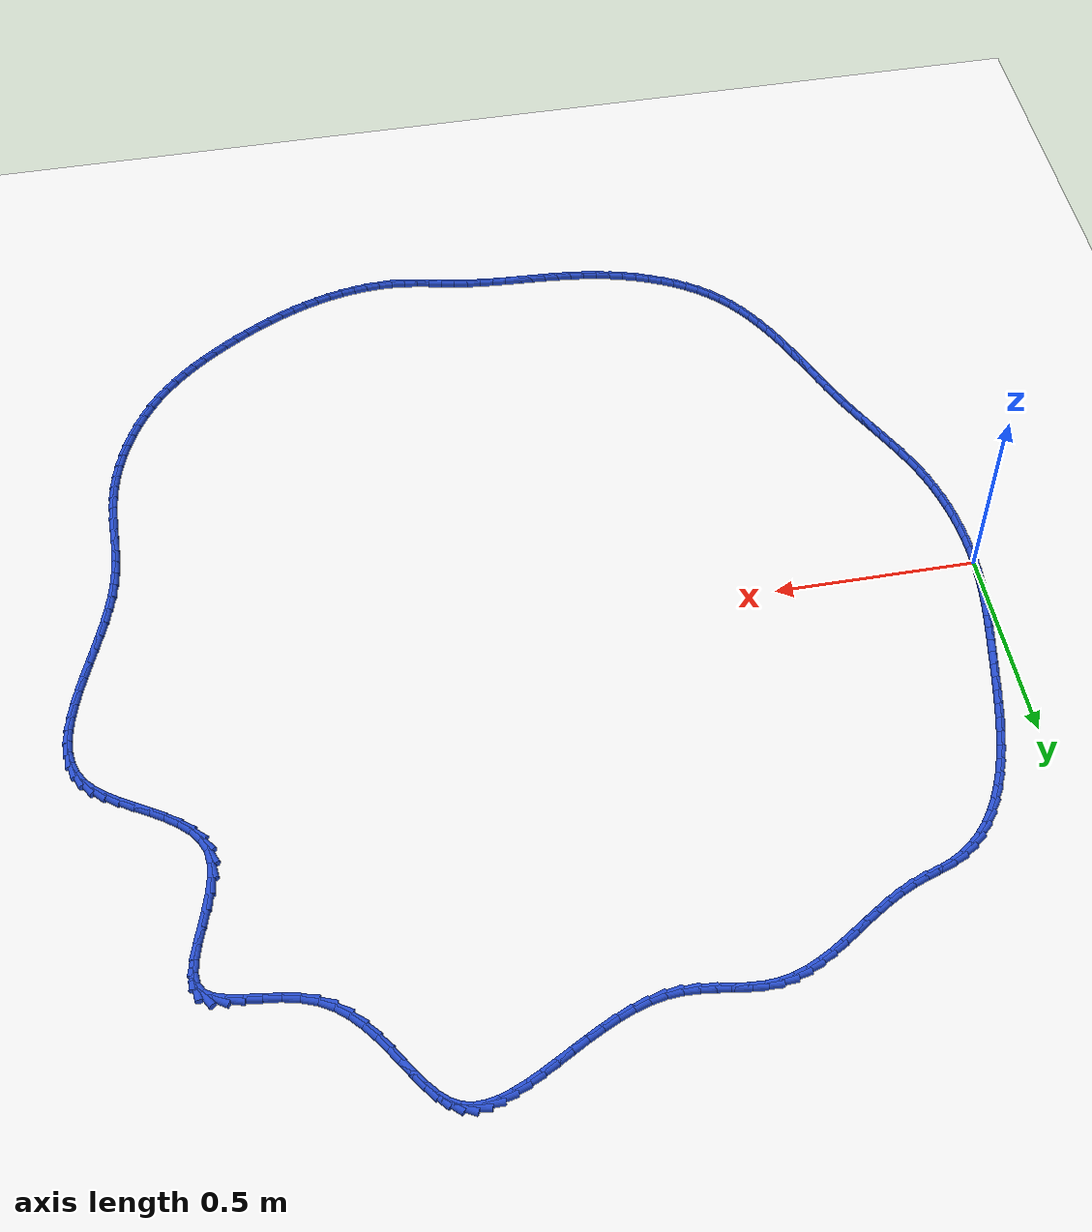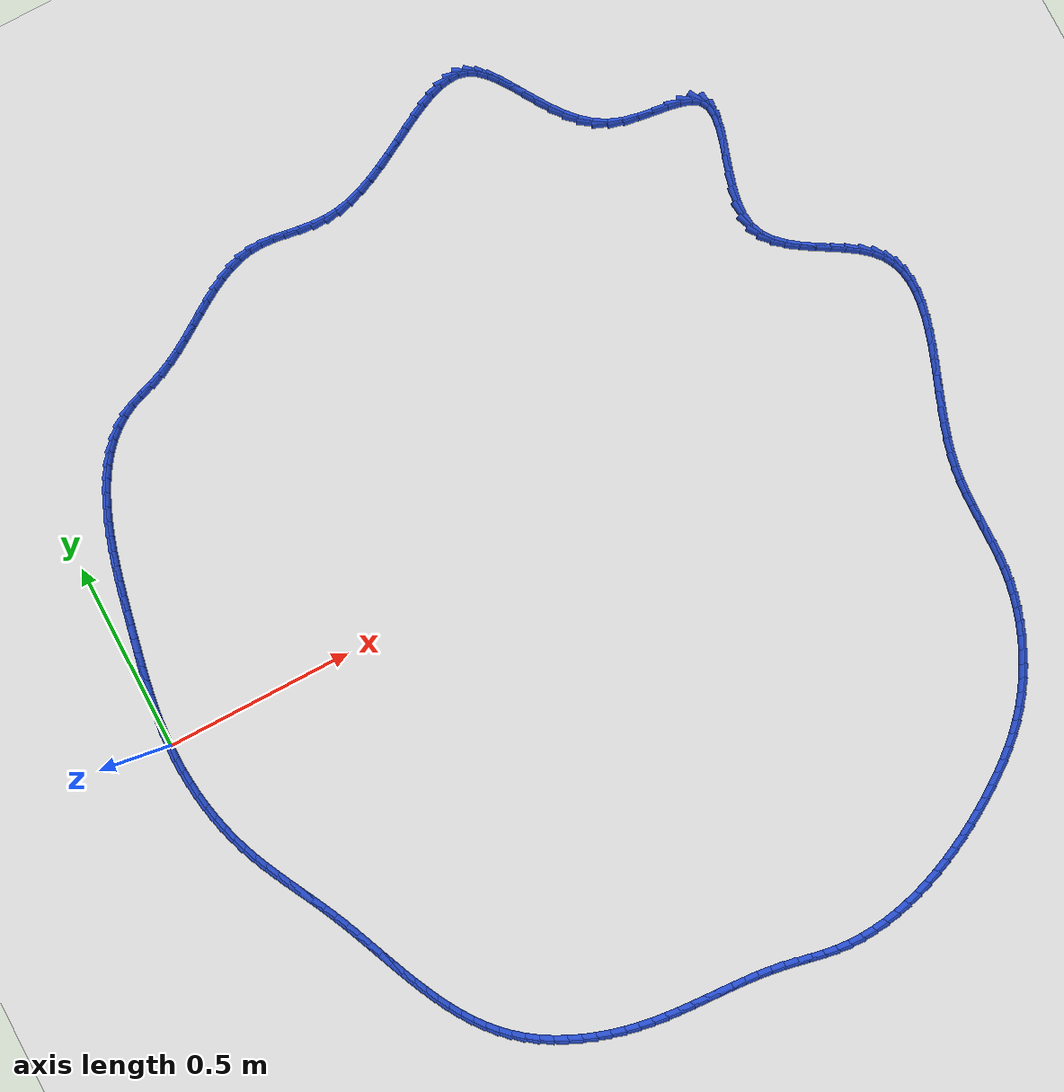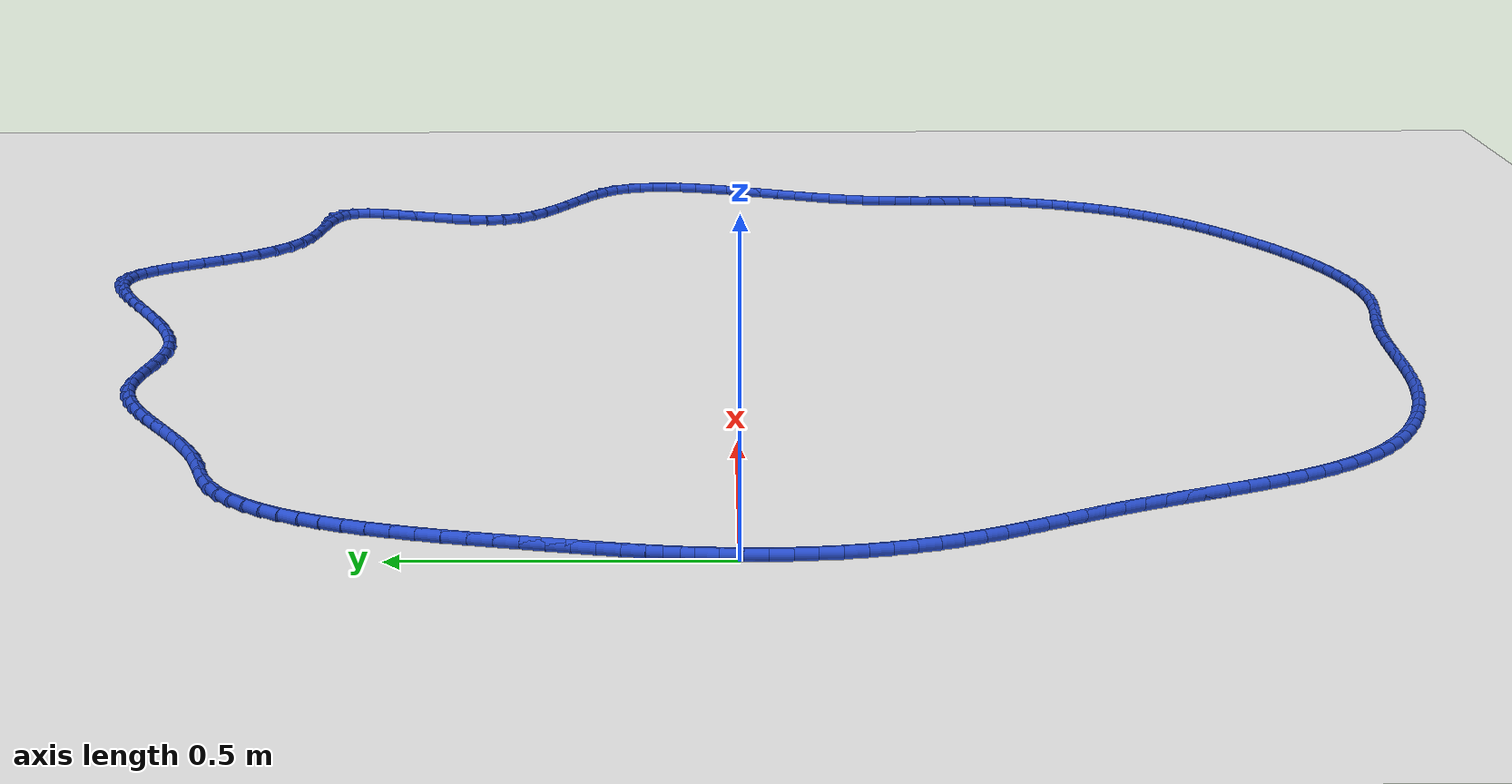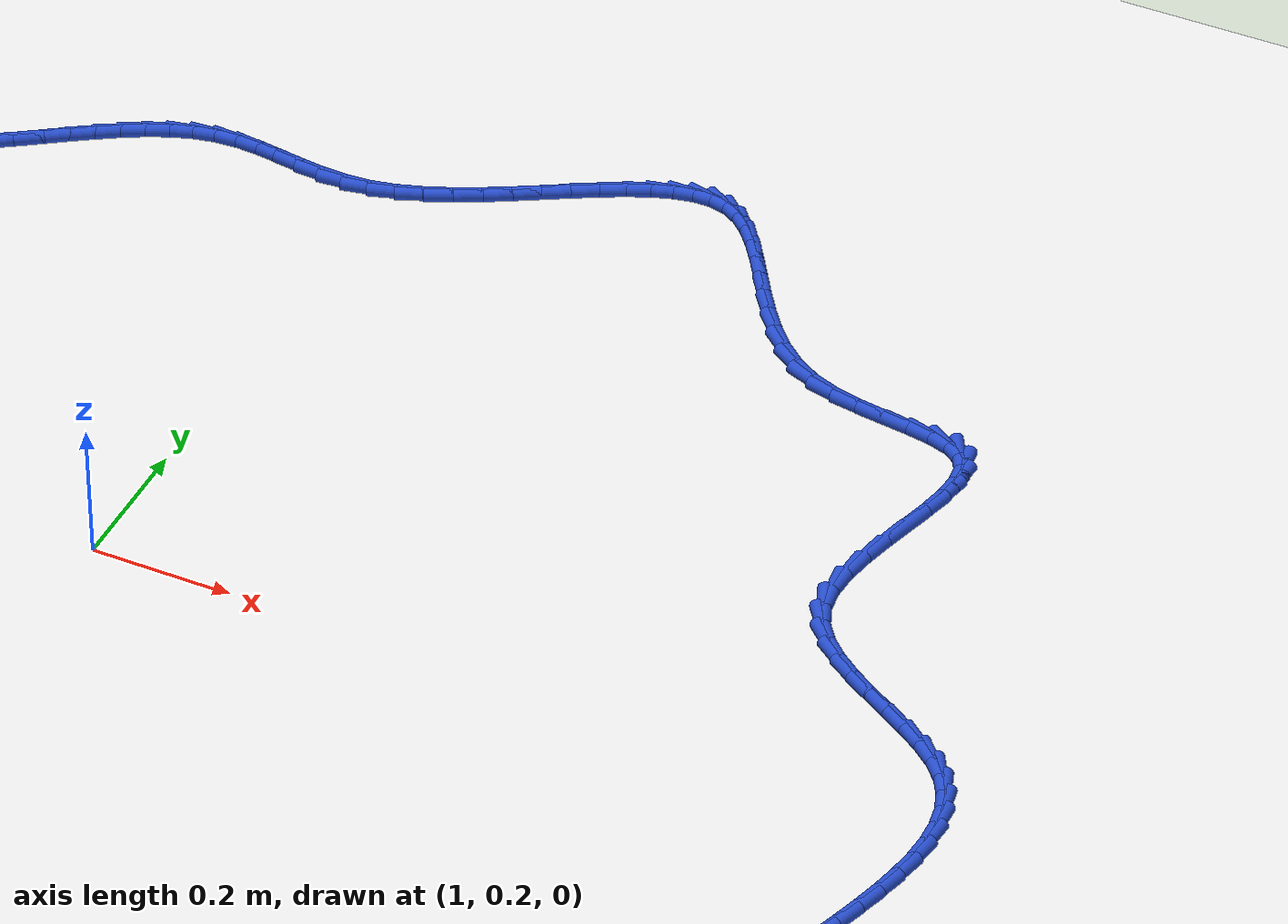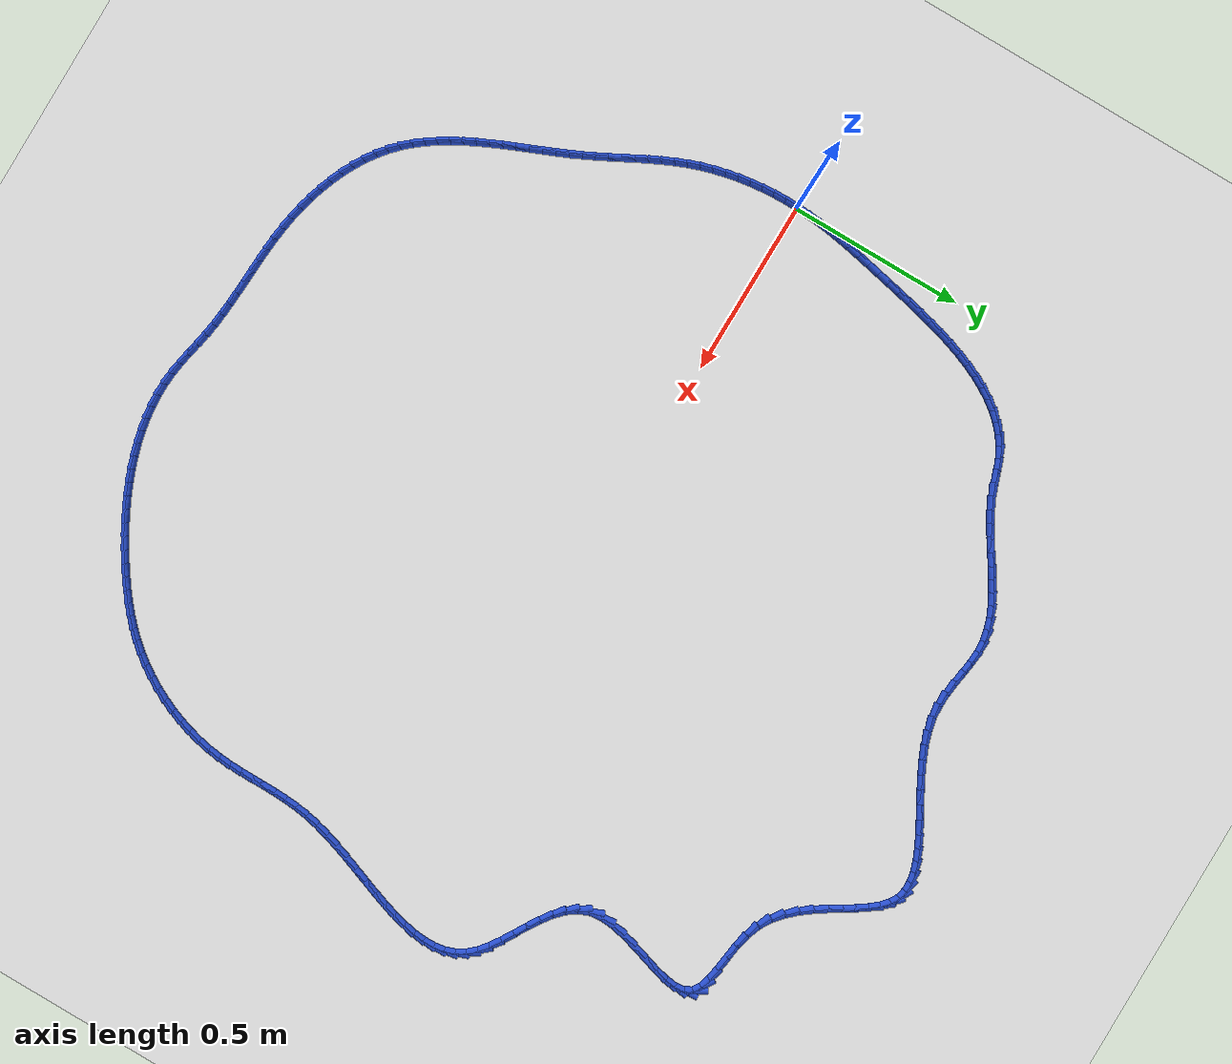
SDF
<sdf version="1.6">
 <world name="default">
  <light name="sun" type="directional">
   <pose>0 0 10 0 -0 0</pose>
   <diffuse>0.8 0.8 0.8 1</diffuse>
   <specular>0.2 0.2 0.2 1</specular>
   <attenuation>
    <range>1000</range>
    <constant>0.9</constant>
    <linear>0.01</linear>
    <quadratic>0.001</quadratic>
   </attenuation>
   <direction>-0.5 0.1 -0.9</direction>
  </light>
  <model name="ground_plane">
   <static>1</static>
   <link name="link">
    <collision name="collision">
     <geometry><plane><normal>0 0 1</normal><size>100 100</size></plane></geometry>
     <surface><friction><ode><mu>100</mu><mu2>50</mu2></ode></friction></surface>
    </collision>
    <visual name="visual">
     <cast_shadows>0</cast_shadows>
     <geometry><plane><normal>0 0 1</normal><size>100 100</size></plane></geometry>
     <material>
      <script><uri>file://media/materials/scripts/gazebo.material</uri><name>Gazebo/WhiteGlow</name></script>
     </material>
    </visual>
   </link>
  </model>
  <gravity>0 0 -9.8</gravity>
  <magnetic_field>6e-06 2.3e-05 -4.2e-05</magnetic_field>
  <atmosphere type="adiabatic"/>
  <physics name="default_physics" default="0" type="ode">
   <max_step_size>0.001</max_step_size>
   <real_time_factor>1</real_time_factor>
   <real_time_update_rate>1000</real_time_update_rate>
  </physics>
  <scene><ambient>0.4 0.4 0.4 1</ambient><background>0.7 0.7 0.7 1</background><shadows>1</shadows></scene>
  <spherical_coordinates>
   <surface_model>EARTH_WGS84</surface_model>
   <latitude_deg>0</latitude_deg>
   <longitude_deg>0</longitude_deg>
   <elevation>0</elevation>
   <heading_deg>0</heading_deg>
  </spherical_coordinates>
  <model name="line">
   <link name="link_0">
    <pose>-5.204170427930421e-18 4.163336342344337e-17 0.01 0 1.57 1.5208849543965577</pose>
    <collision name="collision">
     <geometry><cylinder><radius>0.01</radius><length>0.08</length></cylinder></geometry>
    </collision>
    <visual name="visual">
     <material>
      <script><name>Gazebo/Blue</name><uri>file://media/materials/scripts/gazebo.material</uri></script>
     </material>
     <geometry><cylinder><radius>0.01</radius><length>0.08</length></cylinder></geometry>
    </visual>
   </link>
   <link name="link_1">
    <pose>0.0017199390480877182 0.034431243268915154 0.01 0 1.57 1.4837303100532857</pose>
    <collision name="collision">
     <geometry><cylinder><radius>0.01</radius><length>0.08</length></cylinder></geometry>
    </collision>
    <visual name="visual">
     <material>
      <script><name>Gazebo/Blue</name><uri>file://media/materials/scripts/gazebo.material</uri></script>
     </material>
     <geometry><cylinder><radius>0.01</radius><length>0.08</length></cylinder></geometry>
    </visual>
   </link>
   <link name="link_2">
    <pose>0.004702173828759835 0.06859721846147225 0.01 0 1.57 1.4511710865603584</pose>
    <collision name="collision">
     <geometry><cylinder><radius>0.01</radius><length>0.08</length></cylinder></geometry>
    </collision>
    <visual name="visual">
     <material>
      <script><name>Gazebo/Blue</name><uri>file://media/materials/scripts/gazebo.material</uri></script>
     </material>
     <geometry><cylinder><radius>0.01</radius><length>0.08</length></cylinder></geometry>
    </visual>
   </link>
   <link name="link_3">
    <pose>0.00879488424225968 0.10264663191672037 0.01 0 1.57 1.4236534798670728</pose>
    <collision name="collision">
     <geometry><cylinder><radius>0.01</radius><length>0.08</length></cylinder></geometry>
    </collision>
    <visual name="visual">
     <material>
      <script><name>Gazebo/Blue</name><uri>file://media/materials/scripts/gazebo.material</uri></script>
     </material>
     <geometry><cylinder><radius>0.01</radius><length>0.08</length></cylinder></geometry>
    </visual>
   </link>
   <link name="link_4">
    <pose>0.0138462501888306 0.1367281899737084 0.01 0 1.57 1.4014534340639775</pose>
    <collision name="collision">
     <geometry><cylinder><radius>0.01</radius><length>0.08</length></cylinder></geometry>
    </collision>
    <visual name="visual">
     <material>
      <script><name>Gazebo/Blue</name><uri>file://media/materials/scripts/gazebo.material</uri></script>
     </material>
     <geometry><cylinder><radius>0.01</radius><length>0.08</length></cylinder></geometry>
    </visual>
   </link>
   <link name="link_5">
    <pose>0.019704451568715944 0.17099059897148555 0.01 0 1.57 1.3846882370910742</pose>
    <collision name="collision">
     <geometry><cylinder><radius>0.01</radius><length>0.08</length></cylinder></geometry>
    </collision>
    <visual name="visual">
     <material>
      <script><name>Gazebo/Blue</name><uri>file://media/materials/scripts/gazebo.material</uri></script>
     </material>
     <geometry><cylinder><radius>0.01</radius><length>0.08</length></cylinder></geometry>
    </visual>
   </link>
   <link name="link_6">
    <pose>0.026217668282159032 0.20558256524910065 0.01 0 1.57 1.373335898831359</pose>
    <collision name="collision">
     <geometry><cylinder><radius>0.01</radius><length>0.08</length></cylinder></geometry>
    </collision>
    <visual name="visual">
     <material>
      <script><name>Gazebo/Blue</name><uri>file://media/materials/scripts/gazebo.material</uri></script>
     </material>
     <geometry><cylinder><radius>0.01</radius><length>0.08</length></cylinder></geometry>
    </visual>
   </link>
   <link name="link_7">
    <pose>0.03323408022940323 0.24065279514560292 0.01 0 1.57 1.3672576519073827</pose>
    <collision name="collision">
     <geometry><cylinder><radius>0.01</radius><length>0.08</length></cylinder></geometry>
    </collision>
    <visual name="visual">
     <material>
      <script><name>Gazebo/Blue</name><uri>file://media/materials/scripts/gazebo.material</uri></script>
     </material>
     <geometry><cylinder><radius>0.01</radius><length>0.08</length></cylinder></geometry>
    </visual>
   </link>
   <link name="link_8">
    <pose>0.04060186731069186 0.2763499950000411 0.01 0 1.57 1.3660140015924838</pose>
    <collision name="collision">
     <geometry><cylinder><radius>0.01</radius><length>0.08</length></cylinder></geometry>
    </collision>
    <visual name="visual">
     <material>
      <script><name>Gazebo/Blue</name><uri>file://media/materials/scripts/gazebo.material</uri></script>
     </material>
     <geometry><cylinder><radius>0.01</radius><length>0.08</length></cylinder></geometry>
    </visual>
   </link>
   <link name="link_9">
    <pose>0.04817533305242036 0.31281457818273206 0.01 0 1.57 1.3645071685165557</pose>
    <collision name="collision">
     <geometry><cylinder><radius>0.01</radius><length>0.08</length></cylinder></geometry>
    </collision>
    <visual name="visual">
     <material>
      <script><name>Gazebo/Blue</name><uri>file://media/materials/scripts/gazebo.material</uri></script>
     </material>
     <geometry><cylinder><radius>0.01</radius><length>0.08</length></cylinder></geometry>
    </visual>
   </link>
   <link name="link_10">
    <pose>0.05595473940783197 0.34998929271995866 0.01 0 1.57 1.3578804444189165</pose>
    <collision name="collision">
     <geometry><cylinder><radius>0.01</radius><length>0.08</length></cylinder></geometry>
    </collision>
    <visual name="visual">
     <material>
      <script><name>Gazebo/Blue</name><uri>file://media/materials/scripts/gazebo.material</uri></script>
     </material>
     <geometry><cylinder><radius>0.01</radius><length>0.08</length></cylinder></geometry>
    </visual>
   </link>
   <link name="link_11">
    <pose>0.06408920629358508 0.38761529457383775 0.01 0 1.57 1.3460044763426808</pose>
    <collision name="collision">
     <geometry><cylinder><radius>0.01</radius><length>0.08</length></cylinder></geometry>
    </collision>
    <visual name="visual">
     <material>
      <script><name>Gazebo/Blue</name><uri>file://media/materials/scripts/gazebo.material</uri></script>
     </material>
     <geometry><cylinder><radius>0.01</radius><length>0.08</length></cylinder></geometry>
    </visual>
   </link>
   <link name="link_12">
    <pose>0.07273455723014616 0.4254246612984661 0.01 0 1.57 1.3287923210549824</pose>
    <collision name="collision">
     <geometry><cylinder><radius>0.01</radius><length>0.08</length></cylinder></geometry>
    </collision>
    <visual name="visual">
     <material>
      <script><name>Gazebo/Blue</name><uri>file://media/materials/scripts/gazebo.material</uri></script>
     </material>
     <geometry><cylinder><radius>0.01</radius><length>0.08</length></cylinder></geometry>
    </visual>
   </link>
   <link name="link_13">
    <pose>0.08204661573798165 0.4631494704479401 0.01 0 1.57 1.3059859587979765</pose>
    <collision name="collision">
     <geometry><cylinder><radius>0.01</radius><length>0.08</length></cylinder></geometry>
    </collision>
    <visual name="visual">
     <material>
      <script><name>Gazebo/Blue</name><uri>file://media/materials/scripts/gazebo.material</uri></script>
     </material>
     <geometry><cylinder><radius>0.01</radius><length>0.08</length></cylinder></geometry>
    </visual>
   </link>
   <link name="link_14">
    <pose>0.09218120533755805 0.5005217995763565 0.01 0 1.57 1.2771600559592506</pose>
    <collision name="collision">
     <geometry><cylinder><radius>0.01</radius><length>0.08</length></cylinder></geometry>
    </collision>
    <visual name="visual">
     <material>
      <script><name>Gazebo/Blue</name><uri>file://media/materials/scripts/gazebo.material</uri></script>
     </material>
     <geometry><cylinder><radius>0.01</radius><length>0.08</length></cylinder></geometry>
    </visual>
   </link>
   <link name="link_15">
    <pose>0.10329414954934178 0.5372737262378114 0.01 0 1.57 1.2417213000411023</pose>
    <collision name="collision">
     <geometry><cylinder><radius>0.01</radius><length>0.08</length></cylinder></geometry>
    </collision>
    <visual name="visual">
     <material>
      <script><name>Gazebo/Blue</name><uri>file://media/materials/scripts/gazebo.material</uri></script>
     </material>
     <geometry><cylinder><radius>0.01</radius><length>0.08</length></cylinder></geometry>
    </visual>
   </link>
   <link name="link_16">
    <pose>0.11554127189379927 0.5731373279864014 0.01 0 1.57 1.198908847969215</pose>
    <collision name="collision">
     <geometry><cylinder><radius>0.01</radius><length>0.08</length></cylinder></geometry>
    </collision>
    <visual name="visual">
     <material>
      <script><name>Gazebo/Blue</name><uri>file://media/materials/scripts/gazebo.material</uri></script>
     </material>
     <geometry><cylinder><radius>0.01</radius><length>0.08</length></cylinder></geometry>
    </visual>
   </link>
   <link name="link_17">
    <pose>0.12907839589139705 0.6078446823762234 0.01 0 1.57 1.1478045858629449</pose>
    <collision name="collision">
     <geometry><cylinder><radius>0.01</radius><length>0.08</length></cylinder></geometry>
    </collision>
    <visual name="visual">
     <material>
      <script><name>Gazebo/Blue</name><uri>file://media/materials/scripts/gazebo.material</uri></script>
     </material>
     <geometry><cylinder><radius>0.01</radius><length>0.08</length></cylinder></geometry>
    </visual>
   </link>
   <link name="link_18">
    <pose>0.14406134506260146 0.6411278669613735 0.01 0 1.57 1.0873673313387284</pose>
    <collision name="collision">
     <geometry><cylinder><radius>0.01</radius><length>0.08</length></cylinder></geometry>
    </collision>
    <visual name="visual">
     <material>
      <script><name>Gazebo/Blue</name><uri>file://media/materials/scripts/gazebo.material</uri></script>
     </material>
     <geometry><cylinder><radius>0.01</radius><length>0.08</length></cylinder></geometry>
    </visual>
   </link>
   <link name="link_19">
    <pose>0.16064594292787912 0.6727189592959486 0.01 0 1.57 1.0165126921363037</pose>
    <collision name="collision">
     <geometry><cylinder><radius>0.01</radius><length>0.08</length></cylinder></geometry>
    </collision>
    <visual name="visual">
     <material>
      <script><name>Gazebo/Blue</name><uri>file://media/materials/scripts/gazebo.material</uri></script>
     </material>
     <geometry><cylinder><radius>0.01</radius><length>0.08</length></cylinder></geometry>
    </visual>
   </link>
   <link name="link_20">
    <pose>0.17898801300769623 0.7023500369340444 0.01 0 1.57 0.9342675640775021</pose>
    <collision name="collision">
     <geometry><cylinder><radius>0.01</radius><length>0.08</length></cylinder></geometry>
    </collision>
    <visual name="visual">
     <material>
      <script><name>Gazebo/Blue</name><uri>file://media/materials/scripts/gazebo.material</uri></script>
     </material>
     <geometry><cylinder><radius>0.01</radius><length>0.08</length></cylinder></geometry>
    </visual>
   </link>
   <link name="link_21">
    <pose>0.19924337882251947 0.7297531774297582 0.01 0 1.57 0.8400272031053553</pose>
    <collision name="collision">
     <geometry><cylinder><radius>0.01</radius><length>0.08</length></cylinder></geometry>
    </collision>
    <visual name="visual">
     <material>
      <script><name>Gazebo/Blue</name><uri>file://media/materials/scripts/gazebo.material</uri></script>
     </material>
     <geometry><cylinder><radius>0.01</radius><length>0.08</length></cylinder></geometry>
    </visual>
   </link>
   <link name="link_22">
    <pose>0.2215678638928153 0.7546604583371863 0.01 0 1.57 0.7339170658168073</pose>
    <collision name="collision">
     <geometry><cylinder><radius>0.01</radius><length>0.08</length></cylinder></geometry>
    </collision>
    <visual name="visual">
     <material>
      <script><name>Gazebo/Blue</name><uri>file://media/materials/scripts/gazebo.material</uri></script>
     </material>
     <geometry><cylinder><radius>0.01</radius><length>0.08</length></cylinder></geometry>
    </visual>
   </link>
   <link name="link_23">
    <pose>0.24611729173904995 0.7768039572104251 0.01 0 1.57 0.6171924710068714</pose>
    <collision name="collision">
     <geometry><cylinder><radius>0.01</radius><length>0.08</length></cylinder></geometry>
    </collision>
    <visual name="visual">
     <material>
      <script><name>Gazebo/Blue</name><uri>file://media/materials/scripts/gazebo.material</uri></script>
     </material>
     <geometry><cylinder><radius>0.01</radius><length>0.08</length></cylinder></geometry>
    </visual>
   </link>
   <link name="link_24">
    <pose>0.27304748588169014 0.7959157516035712 0.01 0 1.57 0.49250480300781896</pose>
    <collision name="collision">
     <geometry><cylinder><radius>0.01</radius><length>0.08</length></cylinder></geometry>
    </collision>
    <visual name="visual">
     <material>
      <script><name>Gazebo/Blue</name><uri>file://media/materials/scripts/gazebo.material</uri></script>
     </material>
     <geometry><cylinder><radius>0.01</radius><length>0.08</length></cylinder></geometry>
    </visual>
   </link>
   <link name="link_25">
    <pose>0.3025142698118226 0.8117279191244807 0.01 0 1.57 0.378622844388829</pose>
    <collision name="collision">
     <geometry><cylinder><radius>0.01</radius><length>0.08</length></cylinder></geometry>
    </collision>
    <visual name="visual">
     <material>
      <script><name>Gazebo/Blue</name><uri>file://media/materials/scripts/gazebo.material</uri></script>
     </material>
     <geometry><cylinder><radius>0.01</radius><length>0.08</length></cylinder></geometry>
    </visual>
   </link>
   <link name="link_26">
    <pose>0.33442708786153785 0.8244233725041238 0.01 0 1.57 0.3335779894757052</pose>
    <collision name="collision">
     <geometry><cylinder><radius>0.01</radius><length>0.08</length></cylinder></geometry>
    </collision>
    <visual name="visual">
     <material>
      <script><name>Gazebo/Blue</name><uri>file://media/materials/scripts/gazebo.material</uri></script>
     </material>
     <geometry><cylinder><radius>0.01</radius><length>0.08</length></cylinder></geometry>
    </visual>
   </link>
   <link name="link_27">
    <pose>0.367724383606439 0.835961803188754 0.01 0 1.57 0.36540223435683405</pose>
    <collision name="collision">
     <geometry><cylinder><radius>0.01</radius><length>0.08</length></cylinder></geometry>
    </collision>
    <visual name="visual">
     <material>
      <script><name>Gazebo/Blue</name><uri>file://media/materials/scripts/gazebo.material</uri></script>
     </material>
     <geometry><cylinder><radius>0.01</radius><length>0.08</length></cylinder></geometry>
    </visual>
   </link>
   <link name="link_28">
    <pose>0.4011085047656998 0.8487340036481735 0.01 0 1.57 0.44257388324444397</pose>
    <collision name="collision">
     <geometry><cylinder><radius>0.01</radius><length>0.08</length></cylinder></geometry>
    </collision>
    <visual name="visual">
     <material>
      <script><name>Gazebo/Blue</name><uri>file://media/materials/scripts/gazebo.material</uri></script>
     </material>
     <geometry><cylinder><radius>0.01</radius><length>0.08</length></cylinder></geometry>
    </visual>
   </link>
   <link name="link_29">
    <pose>0.43372339793982173 0.864191137343748 0.01 0 1.57 0.5063381082381144</pose>
    <collision name="collision">
     <geometry><cylinder><radius>0.01</radius><length>0.08</length></cylinder></geometry>
    </collision>
    <visual name="visual">
     <material>
      <script><name>Gazebo/Blue</name><uri>file://media/materials/scripts/gazebo.material</uri></script>
     </material>
     <geometry><cylinder><radius>0.01</radius><length>0.08</length></cylinder></geometry>
    </visual>
   </link>
   <link name="link_30">
    <pose>0.46561058249074977 0.8818745227632787 0.01 0 1.57 0.5505316895759244</pose>
    <collision name="collision">
     <geometry><cylinder><radius>0.01</radius><length>0.08</length></cylinder></geometry>
    </collision>
    <visual name="visual">
     <material>
      <script><name>Gazebo/Blue</name><uri>file://media/materials/scripts/gazebo.material</uri></script>
     </material>
     <geometry><cylinder><radius>0.01</radius><length>0.08</length></cylinder></geometry>
    </visual>
   </link>
   <link name="link_31">
    <pose>0.4969205022887321 0.9010937100816038 0.01 0 1.57 0.5761595144523458</pose>
    <collision name="collision">
     <geometry><cylinder><radius>0.01</radius><length>0.08</length></cylinder></geometry>
    </collision>
    <visual name="visual">
     <material>
      <script><name>Gazebo/Blue</name><uri>file://media/materials/scripts/gazebo.material</uri></script>
     </material>
     <geometry><cylinder><radius>0.01</radius><length>0.08</length></cylinder></geometry>
    </visual>
   </link>
   <link name="link_32">
    <pose>0.5278036012040173 0.921158249473562 0.01 0 1.57 0.5838054190910184</pose>
    <collision name="collision">
     <geometry><cylinder><radius>0.01</radius><length>0.08</length></cylinder></geometry>
    </collision>
    <visual name="visual">
     <material>
      <script><name>Gazebo/Blue</name><uri>file://media/materials/scripts/gazebo.material</uri></script>
     </material>
     <geometry><cylinder><radius>0.01</radius><length>0.08</length></cylinder></geometry>
    </visual>
   </link>
   <link name="link_33">
    <pose>0.5584103231068537 0.9413776911139915 0.01 0 1.57 0.5734031281316788</pose>
    <collision name="collision">
     <geometry><cylinder><radius>0.01</radius><length>0.08</length></cylinder></geometry>
    </collision>
    <visual name="visual">
     <material>
      <script><name>Gazebo/Blue</name><uri>file://media/materials/scripts/gazebo.material</uri></script>
     </material>
     <geometry><cylinder><radius>0.01</radius><length>0.08</length></cylinder></geometry>
    </visual>
   </link>
   <link name="link_34">
    <pose>0.588891111867489 0.9610615851777302 0.01 0 1.57 0.5441404265611153</pose>
    <collision name="collision">
     <geometry><cylinder><radius>0.01</radius><length>0.08</length></cylinder></geometry>
    </collision>
    <visual name="visual">
     <material>
      <script><name>Gazebo/Blue</name><uri>file://media/materials/scripts/gazebo.material</uri></script>
     </material>
     <geometry><cylinder><radius>0.01</radius><length>0.08</length></cylinder></geometry>
    </visual>
   </link>
   <link name="link_35">
    <pose>0.6193964113561725 0.9795194818396171 0.01 0 1.57 0.4944797404890352</pose>
    <collision name="collision">
     <geometry><cylinder><radius>0.01</radius><length>0.08</length></cylinder></geometry>
    </collision>
    <visual name="visual">
     <material>
      <script><name>Gazebo/Blue</name><uri>file://media/materials/scripts/gazebo.material</uri></script>
     </material>
     <geometry><cylinder><radius>0.01</radius><length>0.08</length></cylinder></geometry>
    </visual>
   </link>
   <link name="link_36">
    <pose>0.6500766654431518 0.9960609312744901 0.01 0 1.57 0.4223712786166503</pose>
    <collision name="collision">
     <geometry><cylinder><radius>0.01</radius><length>0.08</length></cylinder></geometry>
    </collision>
    <visual name="visual">
     <material>
      <script><name>Gazebo/Blue</name><uri>file://media/materials/scripts/gazebo.material</uri></script>
     </material>
     <geometry><cylinder><radius>0.01</radius><length>0.08</length></cylinder></geometry>
    </visual>
   </link>
   <link name="link_37">
    <pose>0.6810823179986757 1.0099954836571878 0.01 0 1.57 0.32584374340870803</pose>
    <collision name="collision">
     <geometry><cylinder><radius>0.01</radius><length>0.08</length></cylinder></geometry>
    </collision>
    <visual name="visual">
     <material>
      <script><name>Gazebo/Blue</name><uri>file://media/materials/scripts/gazebo.material</uri></script>
     </material>
     <geometry><cylinder><radius>0.01</radius><length>0.08</length></cylinder></geometry>
    </visual>
   </link>
   <link name="link_38">
    <pose>0.7125638128929924 1.0206326891625483 0.01 0 1.57 0.20420970402357144</pose>
    <collision name="collision">
     <geometry><cylinder><radius>0.01</radius><length>0.08</length></cylinder></geometry>
    </collision>
    <visual name="visual">
     <material>
      <script><name>Gazebo/Blue</name><uri>file://media/materials/scripts/gazebo.material</uri></script>
     </material>
     <geometry><cylinder><radius>0.01</radius><length>0.08</length></cylinder></geometry>
    </visual>
   </link>
   <link name="link_39">
    <pose>0.74467159399635 1.0272820979654098 0.01 0 1.57 0.061967030962383485</pose>
    <collision name="collision">
     <geometry><cylinder><radius>0.01</radius><length>0.08</length></cylinder></geometry>
    </collision>
    <visual name="visual">
     <material>
      <script><name>Gazebo/Blue</name><uri>file://media/materials/scripts/gazebo.material</uri></script>
     </material>
     <geometry><cylinder><radius>0.01</radius><length>0.08</length></cylinder></geometry>
    </visual>
   </link>
   <link name="link_40">
    <pose>0.7775493949081596 1.0293220494198054 0.01 0 1.57 -0.058763496393828954</pose>
    <collision name="collision">
     <geometry><cylinder><radius>0.01</radius><length>0.08</length></cylinder></geometry>
    </collision>
    <visual name="visual">
     <material>
      <script><name>Gazebo/Blue</name><uri>file://media/materials/scripts/gazebo.material</uri></script>
     </material>
     <geometry><cylinder><radius>0.01</radius><length>0.08</length></cylinder></geometry>
    </visual>
   </link>
   <link name="link_41">
    <pose>0.8112229047468861 1.027340995429501 0.01 0 1.57 -0.12666415661157357</pose>
    <collision name="collision">
     <geometry><cylinder><radius>0.01</radius><length>0.08</length></cylinder></geometry>
    </collision>
    <visual name="visual">
     <material>
      <script><name>Gazebo/Blue</name><uri>file://media/materials/scripts/gazebo.material</uri></script>
     </material>
     <geometry><cylinder><radius>0.01</radius><length>0.08</length></cylinder></geometry>
    </visual>
   </link>
   <link name="link_42">
    <pose>0.8456169805940675 1.022961050059529 0.01 0 1.57 -0.14520497904019175</pose>
    <collision name="collision">
     <geometry><cylinder><radius>0.01</radius><length>0.08</length></cylinder></geometry>
    </collision>
    <visual name="visual">
     <material>
      <script><name>Gazebo/Blue</name><uri>file://media/materials/scripts/gazebo.material</uri></script>
     </material>
     <geometry><cylinder><radius>0.01</radius><length>0.08</length></cylinder></geometry>
    </visual>
   </link>
   <link name="link_43">
    <pose>0.8806532385767554 1.0178375514584797 0.01 0 1.57 -0.11775901219655653</pose>
    <collision name="collision">
     <geometry><cylinder><radius>0.01</radius><length>0.08</length></cylinder></geometry>
    </collision>
    <visual name="visual">
     <material>
      <script><name>Gazebo/Blue</name><uri>file://media/materials/scripts/gazebo.material</uri></script>
     </material>
     <geometry><cylinder><radius>0.01</radius><length>0.08</length></cylinder></geometry>
    </visual>
   </link>
   <link name="link_44">
    <pose>0.9162532948220002 1.0136258377749423 0.01 0 1.57 -0.04554335478679585</pose>
    <collision name="collision">
     <geometry><cylinder><radius>0.01</radius><length>0.08</length></cylinder></geometry>
    </collision>
    <visual name="visual">
     <material>
      <script><name>Gazebo/Blue</name><uri>file://media/materials/scripts/gazebo.material</uri></script>
     </material>
     <geometry><cylinder><radius>0.01</radius><length>0.08</length></cylinder></geometry>
    </visual>
   </link>
   <link name="link_45">
    <pose>0.952338765456853 1.0119812471575071 0.01 0 1.57 0.07015226351509476</pose>
    <collision name="collision">
     <geometry><cylinder><radius>0.01</radius><length>0.08</length></cylinder></geometry>
    </collision>
    <visual name="visual">
     <material>
      <script><name>Gazebo/Blue</name><uri>file://media/materials/scripts/gazebo.material</uri></script>
     </material>
     <geometry><cylinder><radius>0.01</radius><length>0.08</length></cylinder></geometry>
    </visual>
   </link>
   <link name="link_46">
    <pose>0.9888307542593755 1.0145454505919485 0.01 0 1.57 0.20118951825141185</pose>
    <collision name="collision">
     <geometry><cylinder><radius>0.01</radius><length>0.08</length></cylinder></geometry>
    </collision>
    <visual name="visual">
     <material>
      <script><name>Gazebo/Blue</name><uri>file://media/materials/scripts/gazebo.material</uri></script>
     </material>
     <geometry><cylinder><radius>0.01</radius><length>0.08</length></cylinder></geometry>
    </visual>
   </link>
   <link name="link_47">
    <pose>1.025616163924477 1.0220477882473606 0.01 0 1.57 0.30696045817694156</pose>
    <collision name="collision">
     <geometry><cylinder><radius>0.01</radius><length>0.08</length></cylinder></geometry>
    </collision>
    <visual name="visual">
     <material>
      <script><name>Gazebo/Blue</name><uri>file://media/materials/scripts/gazebo.material</uri></script>
     </material>
     <geometry><cylinder><radius>0.01</radius><length>0.08</length></cylinder></geometry>
    </visual>
   </link>
   <link name="link_48">
    <pose>1.0625267939365262 1.033747694885121 0.01 0 1.57 0.38700586266564696</pose>
    <collision name="collision">
     <geometry><cylinder><radius>0.01</radius><length>0.08</length></cylinder></geometry>
    </collision>
    <visual name="visual">
     <material>
      <script><name>Gazebo/Blue</name><uri>file://media/materials/scripts/gazebo.material</uri></script>
     </material>
     <geometry><cylinder><radius>0.01</radius><length>0.08</length></cylinder></geometry>
    </visual>
   </link>
   <link name="link_49">
    <pose>1.09938945054746 1.0487714083206872 0.01 0 1.57 0.44498478852891954</pose>
    <collision name="collision">
     <geometry><cylinder><radius>0.01</radius><length>0.08</length></cylinder></geometry>
    </collision>
    <visual name="visual">
     <material>
      <script><name>Gazebo/Blue</name><uri>file://media/materials/scripts/gazebo.material</uri></script>
     </material>
     <geometry><cylinder><radius>0.01</radius><length>0.08</length></cylinder></geometry>
    </visual>
   </link>
   <link name="link_50">
    <pose>1.1360309400092135 1.0662451663695172 0.01 0 1.57 0.4838858919928522</pose>
    <collision name="collision">
     <geometry><cylinder><radius>0.01</radius><length>0.08</length></cylinder></geometry>
    </collision>
    <visual name="visual">
     <material>
      <script><name>Gazebo/Blue</name><uri>file://media/materials/scripts/gazebo.material</uri></script>
     </material>
     <geometry><cylinder><radius>0.01</radius><length>0.08</length></cylinder></geometry>
    </visual>
   </link>
   <link name="link_51">
    <pose>1.1722780685737235 1.085295206847069 0.01 0 1.57 0.5056104026165193</pose>
    <collision name="collision">
     <geometry><cylinder><radius>0.01</radius><length>0.08</length></cylinder></geometry>
    </collision>
    <visual name="visual">
     <material>
      <script><name>Gazebo/Blue</name><uri>file://media/materials/scripts/gazebo.material</uri></script>
     </material>
     <geometry><cylinder><radius>0.01</radius><length>0.08</length></cylinder></geometry>
    </visual>
   </link>
   <link name="link_52">
    <pose>1.2079576424929257 1.1050477675687997 0.01 0 1.57 0.5108276466548389</pose>
    <collision name="collision">
     <geometry><cylinder><radius>0.01</radius><length>0.08</length></cylinder></geometry>
    </collision>
    <visual name="visual">
     <material>
      <script><name>Gazebo/Blue</name><uri>file://media/materials/scripts/gazebo.material</uri></script>
     </material>
     <geometry><cylinder><radius>0.01</radius><length>0.08</length></cylinder></geometry>
    </visual>
   </link>
   <link name="link_53">
    <pose>1.2428964680187569 1.124629086350168 0.01 0 1.57 0.4988321112099095</pose>
    <collision name="collision">
     <geometry><cylinder><radius>0.01</radius><length>0.08</length></cylinder></geometry>
    </collision>
    <visual name="visual">
     <material>
      <script><name>Gazebo/Blue</name><uri>file://media/materials/scripts/gazebo.material</uri></script>
     </material>
     <geometry><cylinder><radius>0.01</radius><length>0.08</length></cylinder></geometry>
    </visual>
   </link>
   <link name="link_54">
    <pose>1.2769213514031528 1.1431654010066314 0.01 0 1.57 0.46725213005288696</pose>
    <collision name="collision">
     <geometry><cylinder><radius>0.01</radius><length>0.08</length></cylinder></geometry>
    </collision>
    <visual name="visual">
     <material>
      <script><name>Gazebo/Blue</name><uri>file://media/materials/scripts/gazebo.material</uri></script>
     </material>
     <geometry><cylinder><radius>0.01</radius><length>0.08</length></cylinder></geometry>
    </visual>
   </link>
   <link name="link_55">
    <pose>1.3098590988980492 1.1597829493536476 0.01 0 1.57 0.4115131672385158</pose>
    <collision name="collision">
     <geometry><cylinder><radius>0.01</radius><length>0.08</length></cylinder></geometry>
    </collision>
    <visual name="visual">
     <material>
      <script><name>Gazebo/Blue</name><uri>file://media/materials/scripts/gazebo.material</uri></script>
     </material>
     <geometry><cylinder><radius>0.01</radius><length>0.08</length></cylinder></geometry>
    </visual>
   </link>
   <link name="link_56">
    <pose>1.3415365167553832 1.1736079692066748 0.01 0 1.57 0.32405297972470215</pose>
    <collision name="collision">
     <geometry><cylinder><radius>0.01</radius><length>0.08</length></cylinder></geometry>
    </collision>
    <visual name="visual">
     <material>
      <script><name>Gazebo/Blue</name><uri>file://media/materials/scripts/gazebo.material</uri></script>
     </material>
     <geometry><cylinder><radius>0.01</radius><length>0.08</length></cylinder></geometry>
    </visual>
   </link>
   <link name="link_57">
    <pose>1.3717804112270906 1.1837666983811703 0.01 0 1.57 0.19374114664384048</pose>
    <collision name="collision">
     <geometry><cylinder><radius>0.01</radius><length>0.08</length></cylinder></geometry>
    </collision>
    <visual name="visual">
     <material>
      <script><name>Gazebo/Blue</name><uri>file://media/materials/scripts/gazebo.material</uri></script>
     </material>
     <geometry><cylinder><radius>0.01</radius><length>0.08</length></cylinder></geometry>
    </visual>
   </link>
   <link name="link_58">
    <pose>1.400417588565107 1.1893853746925929 0.01 0 1.57 0.007627629979824843</pose>
    <collision name="collision">
     <geometry><cylinder><radius>0.01</radius><length>0.08</length></cylinder></geometry>
    </collision>
    <visual name="visual">
     <material>
      <script><name>Gazebo/Blue</name><uri>file://media/materials/scripts/gazebo.material</uri></script>
     </material>
     <geometry><cylinder><radius>0.01</radius><length>0.08</length></cylinder></geometry>
    </visual>
   </link>
   <link name="link_59">
    <pose>1.4272748550213692 1.1895902359563995 0.01 0 1.57 -0.2395548619460163</pose>
    <collision name="collision">
     <geometry><cylinder><radius>0.01</radius><length>0.08</length></cylinder></geometry>
    </collision>
    <visual name="visual">
     <material>
      <script><name>Gazebo/Blue</name><uri>file://media/materials/scripts/gazebo.material</uri></script>
     </material>
     <geometry><cylinder><radius>0.01</radius><length>0.08</length></cylinder></geometry>
    </visual>
   </link>
   <link name="link_60">
    <pose>1.452179016847813 1.1835075199880483 0.01 0 1.57 -0.518976915849766</pose>
    <collision name="collision">
     <geometry><cylinder><radius>0.01</radius><length>0.08</length></cylinder></geometry>
    </collision>
    <visual name="visual">
     <material>
      <script><name>Gazebo/Blue</name><uri>file://media/materials/scripts/gazebo.material</uri></script>
     </material>
     <geometry><cylinder><radius>0.01</radius><length>0.08</length></cylinder></geometry>
    </visual>
   </link>
   <link name="link_61">
    <pose>1.4750266304171653 1.1704568683848118 0.01 0 1.57 -0.7403744451909341</pose>
    <collision name="collision">
     <geometry><cylinder><radius>0.01</radius><length>0.08</length></cylinder></geometry>
    </collision>
    <visual name="visual">
     <material>
      <script><name>Gazebo/Blue</name><uri>file://media/materials/scripts/gazebo.material</uri></script>
     </material>
     <geometry><cylinder><radius>0.01</radius><length>0.08</length></cylinder></geometry>
    </visual>
   </link>
   <link name="link_62">
    <pose>1.496201175592273 1.1511080687132784 0.01 0 1.57 -0.8819455033402076</pose>
    <collision name="collision">
     <geometry><cylinder><radius>0.01</radius><length>0.08</length></cylinder></geometry>
    </collision>
    <visual name="visual">
     <material>
      <script><name>Gazebo/Blue</name><uri>file://media/materials/scripts/gazebo.material</uri></script>
     </material>
     <geometry><cylinder><radius>0.01</radius><length>0.08</length></cylinder></geometry>
    </visual>
   </link>
   <link name="link_63">
    <pose>1.5162936726945122 1.1267063786482425 0.01 0 1.57 -0.963475912575983</pose>
    <collision name="collision">
     <geometry><cylinder><radius>0.01</radius><length>0.08</length></cylinder></geometry>
    </collision>
    <visual name="visual">
     <material>
      <script><name>Gazebo/Blue</name><uri>file://media/materials/scripts/gazebo.material</uri></script>
     </material>
     <geometry><cylinder><radius>0.01</radius><length>0.08</length></cylinder></geometry>
    </visual>
   </link>
   <link name="link_64">
    <pose>1.5358959123936033 1.0984991918935445 0.01 0 1.57 -1.0011606618247737</pose>
    <collision name="collision">
     <geometry><cylinder><radius>0.01</radius><length>0.08</length></cylinder></geometry>
    </collision>
    <visual name="visual">
     <material>
      <script><name>Gazebo/Blue</name><uri>file://media/materials/scripts/gazebo.material</uri></script>
     </material>
     <geometry><cylinder><radius>0.01</radius><length>0.08</length></cylinder></geometry>
    </visual>
   </link>
   <link name="link_65">
    <pose>1.5555996853592713 1.0677339021530254 0.01 0 1.57 -1.004397864008617</pose>
    <collision name="collision">
     <geometry><cylinder><radius>0.01</radius><length>0.08</length></cylinder></geometry>
    </collision>
    <visual name="visual">
     <material>
      <script><name>Gazebo/Blue</name><uri>file://media/materials/scripts/gazebo.material</uri></script>
     </material>
     <geometry><cylinder><radius>0.01</radius><length>0.08</length></cylinder></geometry>
    </visual>
   </link>
   <link name="link_66">
    <pose>1.575996782261238 1.0356579031305253 0.01 0 1.57 -0.977299485223496</pose>
    <collision name="collision">
     <geometry><cylinder><radius>0.01</radius><length>0.08</length></cylinder></geometry>
    </collision>
    <visual name="visual">
     <material>
      <script><name>Gazebo/Blue</name><uri>file://media/materials/scripts/gazebo.material</uri></script>
     </material>
     <geometry><cylinder><radius>0.01</radius><length>0.08</length></cylinder></geometry>
    </visual>
   </link>
   <link name="link_67">
    <pose>1.5976789937692264 1.0035185885298847 0.01 0 1.57 -0.9202476754664713</pose>
    <collision name="collision">
     <geometry><cylinder><radius>0.01</radius><length>0.08</length></cylinder></geometry>
    </collision>
    <visual name="visual">
     <material>
      <script><name>Gazebo/Blue</name><uri>file://media/materials/scripts/gazebo.material</uri></script>
     </material>
     <geometry><cylinder><radius>0.01</radius><length>0.08</length></cylinder></geometry>
    </visual>
   </link>
   <link name="link_68">
    <pose>1.62123811055296 0.9725633520549448 0.01 0 1.57 -0.8311202583945347</pose>
    <collision name="collision">
     <geometry><cylinder><radius>0.01</radius><length>0.08</length></cylinder></geometry>
    </collision>
    <visual name="visual">
     <material>
      <script><name>Gazebo/Blue</name><uri>file://media/materials/scripts/gazebo.material</uri></script>
     </material>
     <geometry><cylinder><radius>0.01</radius><length>0.08</length></cylinder></geometry>
    </visual>
   </link>
   <link name="link_69">
    <pose>1.6472659232821616 0.9440395874095459 0.01 0 1.57 -0.7068810963710302</pose>
    <collision name="collision">
     <geometry><cylinder><radius>0.01</radius><length>0.08</length></cylinder></geometry>
    </collision>
    <visual name="visual">
     <material>
      <script><name>Gazebo/Blue</name><uri>file://media/materials/scripts/gazebo.material</uri></script>
     </material>
     <geometry><cylinder><radius>0.01</radius><length>0.08</length></cylinder></geometry>
    </visual>
   </link>
   <link name="link_70">
    <pose>1.6763542226265533 0.9191946882975285 0.01 0 1.57 -0.5465568833097849</pose>
    <collision name="collision">
     <geometry><cylinder><radius>0.01</radius><length>0.08</length></cylinder></geometry>
    </collision>
    <visual name="visual">
     <material>
      <script><name>Gazebo/Blue</name><uri>file://media/materials/scripts/gazebo.material</uri></script>
     </material>
     <geometry><cylinder><radius>0.01</radius><length>0.08</length></cylinder></geometry>
    </visual>
   </link>
   <link name="link_71">
    <pose>1.7090947992558587 0.8992760484227336 0.01 0 1.57 -0.3636566786226002</pose>
    <collision name="collision">
     <geometry><cylinder><radius>0.01</radius><length>0.08</length></cylinder></geometry>
    </collision>
    <visual name="visual">
     <material>
      <script><name>Gazebo/Blue</name><uri>file://media/materials/scripts/gazebo.material</uri></script>
     </material>
     <geometry><cylinder><radius>0.01</radius><length>0.08</length></cylinder></geometry>
    </visual>
   </link>
   <link name="link_72">
    <pose>1.7458678595486083 0.8852808329219387 0.01 0 1.57 -0.22584856695018668</pose>
    <collision name="collision">
     <geometry><cylinder><radius>0.01</radius><length>0.08</length></cylinder></geometry>
    </collision>
    <visual name="visual">
     <material>
      <script><name>Gazebo/Blue</name><uri>file://media/materials/scripts/gazebo.material</uri></script>
     </material>
     <geometry><cylinder><radius>0.01</radius><length>0.08</length></cylinder></geometry>
    </visual>
   </link>
   <link name="link_73">
    <pose>1.7853624841391937 0.8762062098182672 0.01 0 1.57 -0.1513684330890162</pose>
    <collision name="collision">
     <geometry><cylinder><radius>0.01</radius><length>0.08</length></cylinder></geometry>
    </collision>
    <visual name="visual">
     <material>
      <script><name>Gazebo/Blue</name><uri>file://media/materials/scripts/gazebo.material</uri></script>
     </material>
     <geometry><cylinder><radius>0.01</radius><length>0.08</length></cylinder></geometry>
    </visual>
   </link>
   <link name="link_74">
    <pose>1.825456902207941 0.8700903997748676 0.01 0 1.57 -0.1321057434021316</pose>
    <collision name="collision">
     <geometry><cylinder><radius>0.01</radius><length>0.08</length></cylinder></geometry>
    </collision>
    <visual name="visual">
     <material>
      <script><name>Gazebo/Blue</name><uri>file://media/materials/scripts/gazebo.material</uri></script>
     </material>
     <geometry><cylinder><radius>0.01</radius><length>0.08</length></cylinder></geometry>
    </visual>
   </link>
   <link name="link_75">
    <pose>1.8640242377694036 0.8649655858690671 0.01 0 1.57 -0.17301759444755868</pose>
    <collision name="collision">
     <geometry><cylinder><radius>0.01</radius><length>0.08</length></cylinder></geometry>
    </collision>
    <visual name="visual">
     <material>
      <script><name>Gazebo/Blue</name><uri>file://media/materials/scripts/gazebo.material</uri></script>
     </material>
     <geometry><cylinder><radius>0.01</radius><length>0.08</length></cylinder></geometry>
    </visual>
   </link>
   <link name="link_76">
    <pose>1.8989376148381352 0.8588639511781939 0.01 0 1.57 -0.3010811138258397</pose>
    <collision name="collision">
     <geometry><cylinder><radius>0.01</radius><length>0.08</length></cylinder></geometry>
    </collision>
    <visual name="visual">
     <material>
      <script><name>Gazebo/Blue</name><uri>file://media/materials/scripts/gazebo.material</uri></script>
     </material>
     <geometry><cylinder><radius>0.01</radius><length>0.08</length></cylinder></geometry>
    </visual>
   </link>
   <link name="link_77">
    <pose>1.928070157428688 0.8498176787795755 0.01 0 1.57 -0.5817414018812123</pose>
    <collision name="collision">
     <geometry><cylinder><radius>0.01</radius><length>0.08</length></cylinder></geometry>
    </collision>
    <visual name="visual">
     <material>
      <script><name>Gazebo/Blue</name><uri>file://media/materials/scripts/gazebo.material</uri></script>
     </material>
     <geometry><cylinder><radius>0.01</radius><length>0.08</length></cylinder></geometry>
    </visual>
   </link>
   <link name="link_78">
    <pose>1.9492949895556162 0.8358589517505405 0.01 0 1.57 -1.0566529986468718</pose>
    <collision name="collision">
     <geometry><cylinder><radius>0.01</radius><length>0.08</length></cylinder></geometry>
    </collision>
    <visual name="visual">
     <material>
      <script><name>Gazebo/Blue</name><uri>file://media/materials/scripts/gazebo.material</uri></script>
     </material>
     <geometry><cylinder><radius>0.01</radius><length>0.08</length></cylinder></geometry>
    </visual>
   </link>
   <link name="link_79">
    <pose>1.960890113860649 0.815329743642024 0.01 0 1.57 -1.4635636551070637</pose>
    <collision name="collision">
     <geometry><cylinder><radius>0.01</radius><length>0.08</length></cylinder></geometry>
    </collision>
    <visual name="visual">
     <material>
      <script><name>Gazebo/Blue</name><uri>file://media/materials/scripts/gazebo.material</uri></script>
     </material>
     <geometry><cylinder><radius>0.01</radius><length>0.08</length></cylinder></geometry>
    </visual>
   </link>
   <link name="link_80">
    <pose>1.9637687103272592 0.7885883182755411 0.01 0 1.57 1.449643267915525</pose>
    <collision name="collision">
     <geometry><cylinder><radius>0.01</radius><length>0.08</length></cylinder></geometry>
    </collision>
    <visual name="visual">
     <material>
      <script><name>Gazebo/Blue</name><uri>file://media/materials/scripts/gazebo.material</uri></script>
     </material>
     <geometry><cylinder><radius>0.01</radius><length>0.08</length></cylinder></geometry>
    </visual>
   </link>
   <link name="link_81">
    <pose>1.9598984796846215 0.7567997997495198 0.01 0 1.57 1.3329156102317417</pose>
    <collision name="collision">
     <geometry><cylinder><radius>0.01</radius><length>0.08</length></cylinder></geometry>
    </collision>
    <visual name="visual">
     <material>
      <script><name>Gazebo/Blue</name><uri>file://media/materials/scripts/gazebo.material</uri></script>
     </material>
     <geometry><cylinder><radius>0.01</radius><length>0.08</length></cylinder></geometry>
    </visual>
   </link>
   <link name="link_82">
    <pose>1.9512499153000173 0.7211314489328288 0.01 0 1.57 1.2807234361782398</pose>
    <collision name="collision">
     <geometry><cylinder><radius>0.01</radius><length>0.08</length></cylinder></geometry>
    </collision>
    <visual name="visual">
     <material>
      <script><name>Gazebo/Blue</name><uri>file://media/materials/scripts/gazebo.material</uri></script>
     </material>
     <geometry><cylinder><radius>0.01</radius><length>0.08</length></cylinder></geometry>
    </visual>
   </link>
   <link name="link_83">
    <pose>1.939793510540733 0.682750526694339 0.01 0 1.57 1.272097045706104</pose>
    <collision name="collision">
     <geometry><cylinder><radius>0.01</radius><length>0.08</length></cylinder></geometry>
    </collision>
    <visual name="visual">
     <material>
      <script><name>Gazebo/Blue</name><uri>file://media/materials/scripts/gazebo.material</uri></script>
     </material>
     <geometry><cylinder><radius>0.01</radius><length>0.08</length></cylinder></geometry>
    </visual>
   </link>
   <link name="link_84">
    <pose>1.9274997587740514 0.64282429390292 0.01 0 1.57 1.300656504446641</pose>
    <collision name="collision">
     <geometry><cylinder><radius>0.01</radius><length>0.08</length></cylinder></geometry>
    </collision>
    <visual name="visual">
     <material>
      <script><name>Gazebo/Blue</name><uri>file://media/materials/scripts/gazebo.material</uri></script>
     </material>
     <geometry><cylinder><radius>0.01</radius><length>0.08</length></cylinder></geometry>
    </visual>
   </link>
   <link name="link_85">
    <pose>1.9163391533672571 0.6025200114274408 0.01 0 1.57 1.36965741811731</pose>
    <collision name="collision">
     <geometry><cylinder><radius>0.01</radius><length>0.08</length></cylinder></geometry>
    </collision>
    <visual name="visual">
     <material>
      <script><name>Gazebo/Blue</name><uri>file://media/materials/scripts/gazebo.material</uri></script>
     </material>
     <geometry><cylinder><radius>0.01</radius><length>0.08</length></cylinder></geometry>
    </visual>
   </link>
   <link name="link_86">
    <pose>1.9082821876876341 0.5630049401367724 0.01 0 1.57 1.4915445674172092</pose>
    <collision name="collision">
     <geometry><cylinder><radius>0.01</radius><length>0.08</length></cylinder></geometry>
    </collision>
    <visual name="visual">
     <material>
      <script><name>Gazebo/Blue</name><uri>file://media/materials/scripts/gazebo.material</uri></script>
     </material>
     <geometry><cylinder><radius>0.01</radius><length>0.08</length></cylinder></geometry>
    </visual>
   </link>
   <link name="link_87">
    <pose>1.9052993551024666 0.5254463408997839 0.01 0 1.57 -1.4533836312401527</pose>
    <collision name="collision">
     <geometry><cylinder><radius>0.01</radius><length>0.08</length></cylinder></geometry>
    </collision>
    <visual name="visual">
     <material>
      <script><name>Gazebo/Blue</name><uri>file://media/materials/scripts/gazebo.material</uri></script>
     </material>
     <geometry><cylinder><radius>0.01</radius><length>0.08</length></cylinder></geometry>
    </visual>
   </link>
   <link name="link_88">
    <pose>1.9093611288444055 0.49101146405232304 0.01 0 1.57 -1.1837765858924547</pose>
    <collision name="collision">
     <geometry><cylinder><radius>0.01</radius><length>0.08</length></cylinder></geometry>
    </collision>
    <visual name="visual">
     <material>
      <script><name>Gazebo/Blue</name><uri>file://media/materials/scripts/gazebo.material</uri></script>
     </material>
     <geometry><cylinder><radius>0.01</radius><length>0.08</length></cylinder></geometry>
    </visual>
   </link>
   <link name="link_89">
    <pose>1.9217860438249879 0.46052651171817865 0.01 0 1.57 -0.9385539625949807</pose>
    <collision name="collision">
     <geometry><cylinder><radius>0.01</radius><length>0.08</length></cylinder></geometry>
    </collision>
    <visual name="visual">
     <material>
      <script><name>Gazebo/Blue</name><uri>file://media/materials/scripts/gazebo.material</uri></script>
     </material>
     <geometry><cylinder><radius>0.01</radius><length>0.08</length></cylinder></geometry>
    </visual>
   </link>
   <link name="link_90">
    <pose>1.9415260805542238 0.43357967144024334 0.01 0 1.57 -0.7577896676927874</pose>
    <collision name="collision">
     <geometry><cylinder><radius>0.01</radius><length>0.08</length></cylinder></geometry>
    </collision>
    <visual name="visual">
     <material>
      <script><name>Gazebo/Blue</name><uri>file://media/materials/scripts/gazebo.material</uri></script>
     </material>
     <geometry><cylinder><radius>0.01</radius><length>0.08</length></cylinder></geometry>
    </visual>
   </link>
   <link name="link_91">
    <pose>1.9669963966430708 0.40947830283032277 0.01 0 1.57 -0.6377873316878937</pose>
    <collision name="collision">
     <geometry><cylinder><radius>0.01</radius><length>0.08</length></cylinder></geometry>
    </collision>
    <visual name="visual">
     <material>
      <script><name>Gazebo/Blue</name><uri>file://media/materials/scripts/gazebo.material</uri></script>
     </material>
     <geometry><cylinder><radius>0.01</radius><length>0.08</length></cylinder></geometry>
    </visual>
   </link>
   <link name="link_92">
    <pose>1.9966121497024856 0.38752976550022283 0.01 0 1.57 -0.5670054315671835</pose>
    <collision name="collision">
     <geometry><cylinder><radius>0.01</radius><length>0.08</length></cylinder></geometry>
    </collision>
    <visual name="visual">
     <material>
      <script><name>Gazebo/Blue</name><uri>file://media/materials/scripts/gazebo.material</uri></script>
     </material>
     <geometry><cylinder><radius>0.01</radius><length>0.08</length></cylinder></geometry>
    </visual>
   </link>
   <link name="link_93">
    <pose>2.028788497343424 0.3670414190617495 0.01 0 1.57 -0.5366301315809464</pose>
    <collision name="collision">
     <geometry><cylinder><radius>0.01</radius><length>0.08</length></cylinder></geometry>
    </collision>
    <visual name="visual">
     <material>
      <script><name>Gazebo/Blue</name><uri>file://media/materials/scripts/gazebo.material</uri></script>
     </material>
     <geometry><cylinder><radius>0.01</radius><length>0.08</length></cylinder></geometry>
    </visual>
   </link>
   <link name="link_94">
    <pose>2.061940597176844 0.3473206231267086 0.01 0 1.57 -0.5431282365265463</pose>
    <collision name="collision">
     <geometry><cylinder><radius>0.01</radius><length>0.08</length></cylinder></geometry>
    </collision>
    <visual name="visual">
     <material>
      <script><name>Gazebo/Blue</name><uri>file://media/materials/scripts/gazebo.material</uri></script>
     </material>
     <geometry><cylinder><radius>0.01</radius><length>0.08</length></cylinder></geometry>
    </visual>
   </link>
   <link name="link_95">
    <pose>2.0944836068137023 0.3276747373069057 0.01 0 1.57 -0.588707103175247</pose>
    <collision name="collision">
     <geometry><cylinder><radius>0.01</radius><length>0.08</length></cylinder></geometry>
    </collision>
    <visual name="visual">
     <material>
      <script><name>Gazebo/Blue</name><uri>file://media/materials/scripts/gazebo.material</uri></script>
     </material>
     <geometry><cylinder><radius>0.01</radius><length>0.08</length></cylinder></geometry>
    </visual>
   </link>
   <link name="link_96">
    <pose>2.1248326838649554 0.307411121214147 0.01 0 1.57 -0.6819903881005013</pose>
    <collision name="collision">
     <geometry><cylinder><radius>0.01</radius><length>0.08</length></cylinder></geometry>
    </collision>
    <visual name="visual">
     <material>
      <script><name>Gazebo/Blue</name><uri>file://media/materials/scripts/gazebo.material</uri></script>
     </material>
     <geometry><cylinder><radius>0.01</radius><length>0.08</length></cylinder></geometry>
    </visual>
   </link>
   <link name="link_97">
    <pose>2.1514029859415613 0.2858371344602384 0.01 0 1.57 -0.8374402632788893</pose>
    <collision name="collision">
     <geometry><cylinder><radius>0.01</radius><length>0.08</length></cylinder></geometry>
    </collision>
    <visual name="visual">
     <material>
      <script><name>Gazebo/Blue</name><uri>file://media/materials/scripts/gazebo.material</uri></script>
     </material>
     <geometry><cylinder><radius>0.01</radius><length>0.08</length></cylinder></geometry>
    </visual>
   </link>
   <link name="link_98">
    <pose>2.1726356882173277 0.26227089405142234 0.01 0 1.57 -1.037929057153234</pose>
    <collision name="collision">
     <geometry><cylinder><radius>0.01</radius><length>0.08</length></cylinder></geometry>
    </collision>
    <visual name="visual">
     <material>
      <script><name>Gazebo/Blue</name><uri>file://media/materials/scripts/gazebo.material</uri></script>
     </material>
     <geometry><cylinder><radius>0.01</radius><length>0.08</length></cylinder></geometry>
    </visual>
   </link>
   <link name="link_99">
    <pose>2.1878881867380278 0.23640934376442818 0.01 0 1.57 -1.2350364702051757</pose>
    <collision name="collision">
     <geometry><cylinder><radius>0.01</radius><length>0.08</length></cylinder></geometry>
    </collision>
    <visual name="visual">
     <material>
      <script><name>Gazebo/Blue</name><uri>file://media/materials/scripts/gazebo.material</uri></script>
     </material>
     <geometry><cylinder><radius>0.01</radius><length>0.08</length></cylinder></geometry>
    </visual>
   </link>
   <link name="link_100">
    <pose>2.1976557543018718 0.20841990145983041 0.01 0 1.57 -1.4101335996323903</pose>
    <collision name="collision">
     <geometry><cylinder><radius>0.01</radius><length>0.08</length></cylinder></geometry>
    </collision>
    <visual name="visual">
     <material>
      <script><name>Gazebo/Blue</name><uri>file://media/materials/scripts/gazebo.material</uri></script>
     </material>
     <geometry><cylinder><radius>0.01</radius><length>0.08</length></cylinder></geometry>
    </visual>
   </link>
   <link name="link_101">
    <pose>2.202504665816266 0.1784993420021169 0.01 0 1.57 -1.5551118789373677</pose>
    <collision name="collision">
     <geometry><cylinder><radius>0.01</radius><length>0.08</length></cylinder></geometry>
    </collision>
    <visual name="visual">
     <material>
      <script><name>Gazebo/Blue</name><uri>file://media/materials/scripts/gazebo.material</uri></script>
     </material>
     <geometry><cylinder><radius>0.01</radius><length>0.08</length></cylinder></geometry>
    </visual>
   </link>
   <link name="link_102">
    <pose>2.203001196188615 0.1468444402557766 0.01 0 1.57 1.472012811061894</pose>
    <collision name="collision">
     <geometry><cylinder><radius>0.01</radius><length>0.08</length></cylinder></geometry>
    </collision>
    <visual name="visual">
     <material>
      <script><name>Gazebo/Blue</name><uri>file://media/materials/scripts/gazebo.material</uri></script>
     </material>
     <geometry><cylinder><radius>0.01</radius><length>0.08</length></cylinder></geometry>
    </visual>
   </link>
   <link name="link_103">
    <pose>2.1997116203263243 0.11365197108529741 0.01 0 1.57 1.38448566436017</pose>
    <collision name="collision">
     <geometry><cylinder><radius>0.01</radius><length>0.08</length></cylinder></geometry>
    </collision>
    <visual name="visual">
     <material>
      <script><name>Gazebo/Blue</name><uri>file://media/materials/scripts/gazebo.material</uri></script>
     </material>
     <geometry><cylinder><radius>0.01</radius><length>0.08</length></cylinder></geometry>
    </visual>
   </link>
   <link name="link_104">
    <pose>2.1932022131367996 0.07911870935516763 0.01 0 1.57 1.3194006736147386</pose>
    <collision name="collision">
     <geometry><cylinder><radius>0.01</radius><length>0.08</length></cylinder></geometry>
    </collision>
    <visual name="visual">
     <material>
      <script><name>Gazebo/Blue</name><uri>file://media/materials/scripts/gazebo.material</uri></script>
     </material>
     <geometry><cylinder><radius>0.01</radius><length>0.08</length></cylinder></geometry>
    </visual>
   </link>
   <link name="link_105">
    <pose>2.184039249527447 0.04344142992987551 0.01 0 1.57 1.272767349405304</pose>
    <collision name="collision">
     <geometry><cylinder><radius>0.01</radius><length>0.08</length></cylinder></geometry>
    </collision>
    <visual name="visual">
     <material>
      <script><name>Gazebo/Blue</name><uri>file://media/materials/scripts/gazebo.material</uri></script>
     </material>
     <geometry><cylinder><radius>0.01</radius><length>0.08</length></cylinder></geometry>
    </visual>
   </link>
   <link name="link_106">
    <pose>2.172789004405671 0.006816907673908357 0.01 0 1.57 1.241529554036133</pose>
    <collision name="collision">
     <geometry><cylinder><radius>0.01</radius><length>0.08</length></cylinder></geometry>
    </collision>
    <visual name="visual">
     <material>
      <script><name>Gazebo/Blue</name><uri>file://media/materials/scripts/gazebo.material</uri></script>
     </material>
     <geometry><cylinder><radius>0.01</radius><length>0.08</length></cylinder></geometry>
    </visual>
   </link>
   <link name="link_107">
    <pose>2.160017752678877 -0.03055808254824373 0.01 0 1.57 1.2235692440288508</pose>
    <collision name="collision">
     <geometry><cylinder><radius>0.01</radius><length>0.08</length></cylinder></geometry>
    </collision>
    <visual name="visual">
     <material>
      <script><name>Gazebo/Blue</name><uri>file://media/materials/scripts/gazebo.material</uri></script>
     </material>
     <geometry><cylinder><radius>0.01</radius><length>0.08</length></cylinder></geometry>
    </visual>
   </link>
   <link name="link_108">
    <pose>2.146291769254472 -0.0684867658720934 0.01 0 1.57 1.2175939475428124</pose>
    <collision name="collision">
     <geometry><cylinder><radius>0.01</radius><length>0.08</length></cylinder></geometry>
    </collision>
    <visual name="visual">
     <material>
      <script><name>Gazebo/Blue</name><uri>file://media/materials/scripts/gazebo.material</uri></script>
     </material>
     <geometry><cylinder><radius>0.01</radius><length>0.08</length></cylinder></geometry>
    </visual>
   </link>
   <link name="link_109">
    <pose>2.132177329039859 -0.1067723674331524 0.01 0 1.57 1.2230284294908644</pose>
    <collision name="collision">
     <geometry><cylinder><radius>0.01</radius><length>0.08</length></cylinder></geometry>
    </collision>
    <visual name="visual">
     <material>
      <script><name>Gazebo/Blue</name><uri>file://media/materials/scripts/gazebo.material</uri></script>
     </material>
     <geometry><cylinder><radius>0.01</radius><length>0.08</length></cylinder></geometry>
    </visual>
   </link>
   <link name="link_110">
    <pose>2.118240706942446 -0.14521811236693252 0.01 0 1.57 1.239947168437429</pose>
    <collision name="collision">
     <geometry><cylinder><radius>0.01</radius><length>0.08</length></cylinder></geometry>
    </collision>
    <visual name="visual">
     <material>
      <script><name>Gazebo/Blue</name><uri>file://media/materials/scripts/gazebo.material</uri></script>
     </material>
     <geometry><cylinder><radius>0.01</radius><length>0.08</length></cylinder></geometry>
    </visual>
   </link>
   <link name="link_111">
    <pose>2.105048177869637 -0.18362722580894542 0.01 0 1.57 1.2690513146308564</pose>
    <collision name="collision">
     <geometry><cylinder><radius>0.01</radius><length>0.08</length></cylinder></geometry>
    </collision>
    <visual name="visual">
     <material>
      <script><name>Gazebo/Blue</name><uri>file://media/materials/scripts/gazebo.material</uri></script>
     </material>
     <geometry><cylinder><radius>0.01</radius><length>0.08</length></cylinder></geometry>
    </visual>
   </link>
   <link name="link_112">
    <pose>2.093166016728837 -0.2218029328947037 0.01 0 1.57 1.3116774733507754</pose>
    <collision name="collision">
     <geometry><cylinder><radius>0.01</radius><length>0.08</length></cylinder></geometry>
    </collision>
    <visual name="visual">
     <material>
      <script><name>Gazebo/Blue</name><uri>file://media/materials/scripts/gazebo.material</uri></script>
     </material>
     <geometry><cylinder><radius>0.01</radius><length>0.08</length></cylinder></geometry>
    </visual>
   </link>
   <link name="link_113">
    <pose>2.0831604984274525 -0.25954845875971744 0.01 0 1.57 1.3696706463029527</pose>
    <collision name="collision">
     <geometry><cylinder><radius>0.01</radius><length>0.08</length></cylinder></geometry>
    </collision>
    <visual name="visual">
     <material>
      <script><name>Gazebo/Blue</name><uri>file://media/materials/scripts/gazebo.material</uri></script>
     </material>
     <geometry><cylinder><radius>0.01</radius><length>0.08</length></cylinder></geometry>
    </visual>
   </link>
   <link name="link_114">
    <pose>2.075592385623981 -0.296668478698411 0.01 0 1.57 1.4350132281158823</pose>
    <collision name="collision">
     <geometry><cylinder><radius>0.01</radius><length>0.08</length></cylinder></geometry>
    </collision>
    <visual name="visual">
     <material>
      <script><name>Gazebo/Blue</name><uri>file://media/materials/scripts/gazebo.material</uri></script>
     </material>
     <geometry><cylinder><radius>0.01</radius><length>0.08</length></cylinder></geometry>
    </visual>
   </link>
   <link name="link_115">
    <pose>2.0706185356796416 -0.33307392715207945 0.01 0 1.57 1.4900600043595091</pose>
    <collision name="collision">
     <geometry><cylinder><radius>0.01</radius><length>0.08</length></cylinder></geometry>
    </collision>
    <visual name="visual">
     <material>
      <script><name>Gazebo/Blue</name><uri>file://media/materials/scripts/gazebo.material</uri></script>
     </material>
     <geometry><cylinder><radius>0.01</radius><length>0.08</length></cylinder></geometry>
    </visual>
   </link>
   <link name="link_116">
    <pose>2.0677236059931485 -0.36885258049755093 0.01 0 1.57 1.5312516894622321</pose>
    <collision name="collision">
     <geometry><cylinder><radius>0.01</radius><length>0.08</length></cylinder></geometry>
    </collision>
    <visual name="visual">
     <material>
      <script><name>Gazebo/Blue</name><uri>file://media/materials/scripts/gazebo.material</uri></script>
     </material>
     <geometry><cylinder><radius>0.01</radius><length>0.08</length></cylinder></geometry>
    </visual>
   </link>
   <link name="link_117">
    <pose>2.066328678831707 -0.40410894041652673 0.01 0 1.57 1.5571960791776056</pose>
    <collision name="collision">
     <geometry><cylinder><radius>0.01</radius><length>0.08</length></cylinder></geometry>
    </collision>
    <visual name="visual">
     <material>
      <script><name>Gazebo/Blue</name><uri>file://media/materials/scripts/gazebo.material</uri></script>
     </material>
     <geometry><cylinder><radius>0.01</radius><length>0.08</length></cylinder></geometry>
    </visual>
   </link>
   <link name="link_118">
    <pose>2.0658548364625204 -0.43894750859070786 0.01 0 1.57 1.5669824640687755</pose>
    <collision name="collision">
     <geometry><cylinder><radius>0.01</radius><length>0.08</length></cylinder></geometry>
    </collision>
    <visual name="visual">
     <material>
      <script><name>Gazebo/Blue</name><uri>file://media/materials/scripts/gazebo.material</uri></script>
     </material>
     <geometry><cylinder><radius>0.01</radius><length>0.08</length></cylinder></geometry>
    </visual>
   </link>
   <link name="link_119">
    <pose>2.065723161152793 -0.4734727867017963 0.01 0 1.57 1.5600606183499888</pose>
    <collision name="collision">
     <geometry><cylinder><radius>0.01</radius><length>0.08</length></cylinder></geometry>
    </collision>
    <visual name="visual">
     <material>
      <script><name>Gazebo/Blue</name><uri>file://media/materials/scripts/gazebo.material</uri></script>
     </material>
     <geometry><cylinder><radius>0.01</radius><length>0.08</length></cylinder></geometry>
    </visual>
   </link>
   <link name="link_120">
    <pose>2.065354735169728 -0.5077892764314915 0.01 0 1.57 1.5361998429123054</pose>
    <collision name="collision">
     <geometry><cylinder><radius>0.01</radius><length>0.08</length></cylinder></geometry>
    </collision>
    <visual name="visual">
     <material>
      <script><name>Gazebo/Blue</name><uri>file://media/materials/scripts/gazebo.material</uri></script>
     </material>
     <geometry><cylinder><radius>0.01</radius><length>0.08</length></cylinder></geometry>
    </visual>
   </link>
   <link name="link_121">
    <pose>2.06417064078053 -0.5420014794614955 0.01 0 1.57 1.4955659261661765</pose>
    <collision name="collision">
     <geometry><cylinder><radius>0.01</radius><length>0.08</length></cylinder></geometry>
    </collision>
    <visual name="visual">
     <material>
      <script><name>Gazebo/Blue</name><uri>file://media/materials/scripts/gazebo.material</uri></script>
     </material>
     <geometry><cylinder><radius>0.01</radius><length>0.08</length></cylinder></geometry>
    </visual>
   </link>
   <link name="link_122">
    <pose>2.061591960252401 -0.5762138974735092 0.01 0 1.57 1.4395167184632929</pose>
    <collision name="collision">
     <geometry><cylinder><radius>0.01</radius><length>0.08</length></cylinder></geometry>
    </collision>
    <visual name="visual">
     <material>
      <script><name>Gazebo/Blue</name><uri>file://media/materials/scripts/gazebo.material</uri></script>
     </material>
     <geometry><cylinder><radius>0.01</radius><length>0.08</length></cylinder></geometry>
    </visual>
   </link>
   <link name="link_123">
    <pose>2.0570620439866487 -0.6105213044536851 0.01 0 1.57 1.3784179722360077</pose>
    <collision name="collision">
     <geometry><cylinder><radius>0.01</radius><length>0.08</length></cylinder></geometry>
    </collision>
    <visual name="visual">
     <material>
      <script><name>Gazebo/Blue</name><uri>file://media/materials/scripts/gazebo.material</uri></script>
     </material>
     <geometry><cylinder><radius>0.01</radius><length>0.08</length></cylinder></geometry>
    </visual>
   </link>
   <link name="link_124">
    <pose>2.050372027196258 -0.6448665467615043 0.01 0 1.57 1.319439212764857</pose>
    <collision name="collision">
     <geometry><cylinder><radius>0.01</radius><length>0.08</length></cylinder></geometry>
    </collision>
    <visual name="visual">
     <material>
      <script><name>Gazebo/Blue</name><uri>file://media/materials/scripts/gazebo.material</uri></script>
     </material>
     <geometry><cylinder><radius>0.01</radius><length>0.08</length></cylinder></geometry>
    </visual>
   </link>
   <link name="link_125">
    <pose>2.0415884331198746 -0.6790721692143837 0.01 0 1.57 1.262169212749637</pose>
    <collision name="collision">
     <geometry><cylinder><radius>0.01</radius><length>0.08</length></cylinder></geometry>
    </collision>
    <visual name="visual">
     <material>
      <script><name>Gazebo/Blue</name><uri>file://media/materials/scripts/gazebo.material</uri></script>
     </material>
     <geometry><cylinder><radius>0.01</radius><length>0.08</length></cylinder></geometry>
    </visual>
   </link>
   <link name="link_126">
    <pose>2.0307853260558293 -0.712957422364831 0.01 0 1.57 1.2060122009495136</pose>
    <collision name="collision">
     <geometry><cylinder><radius>0.01</radius><length>0.08</length></cylinder></geometry>
    </collision>
    <visual name="visual">
     <material>
      <script><name>Gazebo/Blue</name><uri>file://media/materials/scripts/gazebo.material</uri></script>
     </material>
     <geometry><cylinder><radius>0.01</radius><length>0.08</length></cylinder></geometry>
    </visual>
   </link>
   <link name="link_127">
    <pose>2.0180367703024498 -0.7463415567653549 0.01 0 1.57 1.1503883381426177</pose>
    <collision name="collision">
     <geometry><cylinder><radius>0.01</radius><length>0.08</length></cylinder></geometry>
    </collision>
    <visual name="visual">
     <material>
      <script><name>Gazebo/Blue</name><uri>file://media/materials/scripts/gazebo.material</uri></script>
     </material>
     <geometry><cylinder><radius>0.01</radius><length>0.08</length></cylinder></geometry>
    </visual>
   </link>
   <link name="link_128">
    <pose>2.0034168301580655 -0.7790438229684645 0.01 0 1.57 1.0947284491717477</pose>
    <collision name="collision">
     <geometry><cylinder><radius>0.01</radius><length>0.08</length></cylinder></geometry>
    </collision>
    <visual name="visual">
     <material>
      <script><name>Gazebo/Blue</name><uri>file://media/materials/scripts/gazebo.material</uri></script>
     </material>
     <geometry><cylinder><radius>0.01</radius><length>0.08</length></cylinder></geometry>
    </visual>
   </link>
   <link name="link_129">
    <pose>1.9869995699210063 -0.8108834715266688 0.01 0 1.57 1.0384680142832199</pose>
    <collision name="collision">
     <geometry><cylinder><radius>0.01</radius><length>0.08</length></cylinder></geometry>
    </collision>
    <visual name="visual">
     <material>
      <script><name>Gazebo/Blue</name><uri>file://media/materials/scripts/gazebo.material</uri></script>
     </material>
     <geometry><cylinder><radius>0.01</radius><length>0.08</length></cylinder></geometry>
    </visual>
   </link>
   <link name="link_130">
    <pose>1.968859053889602 -0.8416797529924764 0.01 0 1.57 0.9810415824294428</pose>
    <collision name="collision">
     <geometry><cylinder><radius>0.01</radius><length>0.08</length></cylinder></geometry>
    </collision>
    <visual name="visual">
     <material>
      <script><name>Gazebo/Blue</name><uri>file://media/materials/scripts/gazebo.material</uri></script>
     </material>
     <geometry><cylinder><radius>0.01</radius><length>0.08</length></cylinder></geometry>
    </visual>
   </link>
   <link name="link_131">
    <pose>1.949069346362181 -0.8712519179183962 0.01 0 1.57 0.9218787624622179</pose>
    <collision name="collision">
     <geometry><cylinder><radius>0.01</radius><length>0.08</length></cylinder></geometry>
    </collision>
    <visual name="visual">
     <material>
      <script><name>Gazebo/Blue</name><uri>file://media/materials/scripts/gazebo.material</uri></script>
     </material>
     <geometry><cylinder><radius>0.01</radius><length>0.08</length></cylinder></geometry>
    </visual>
   </link>
   <link name="link_132">
    <pose>1.9277045116370732 -0.8994192168569375 0.01 0 1.57 0.8609638166483321</pose>
    <collision name="collision">
     <geometry><cylinder><radius>0.01</radius><length>0.08</length></cylinder></geometry>
    </collision>
    <visual name="visual">
     <material>
      <script><name>Gazebo/Blue</name><uri>file://media/materials/scripts/gazebo.material</uri></script>
     </material>
     <geometry><cylinder><radius>0.01</radius><length>0.08</length></cylinder></geometry>
    </visual>
   </link>
   <link name="link_133">
    <pose>1.904841227279127 -0.9260280240328463 0.01 0 1.57 0.8024733586764066</pose>
    <collision name="collision">
     <geometry><cylinder><radius>0.01</radius><length>0.08</length></cylinder></geometry>
    </collision>
    <visual name="visual">
     <material>
      <script><name>Gazebo/Blue</name><uri>file://media/materials/scripts/gazebo.material</uri></script>
     </material>
     <geometry><cylinder><radius>0.01</radius><length>0.08</length></cylinder></geometry>
    </visual>
   </link>
   <link name="link_134">
    <pose>1.880576514487603 -0.9511358647601564 0.01 0 1.57 0.7489972754235198</pose>
    <collision name="collision">
     <geometry><cylinder><radius>0.01</radius><length>0.08</length></cylinder></geometry>
    </collision>
    <visual name="visual">
     <material>
      <script><name>Gazebo/Blue</name><uri>file://media/materials/scripts/gazebo.material</uri></script>
     </material>
     <geometry><cylinder><radius>0.01</radius><length>0.08</length></cylinder></geometry>
    </visual>
   </link>
   <link name="link_135">
    <pose>1.8550169317616545 -0.9748992541017447 0.01 0 1.57 0.7010188673986253</pose>
    <collision name="collision">
     <geometry><cylinder><radius>0.01</radius><length>0.08</length></cylinder></geometry>
    </collision>
    <visual name="visual">
     <material>
      <script><name>Gazebo/Blue</name><uri>file://media/materials/scripts/gazebo.material</uri></script>
     </material>
     <geometry><cylinder><radius>0.01</radius><length>0.08</length></cylinder></geometry>
    </visual>
   </link>
   <link name="link_136">
    <pose>1.8282690923387488 -0.997475275261558 0.01 0 1.57 0.6588134519586387</pose>
    <collision name="collision">
     <geometry><cylinder><radius>0.01</radius><length>0.08</length></cylinder></geometry>
    </collision>
    <visual name="visual">
     <material>
      <script><name>Gazebo/Blue</name><uri>file://media/materials/scripts/gazebo.material</uri></script>
     </material>
     <geometry><cylinder><radius>0.01</radius><length>0.08</length></cylinder></geometry>
    </visual>
   </link>
   <link name="link_137">
    <pose>1.8004396094563502 -1.019021011443542 0.01 0 1.57 0.6224960009613689</pose>
    <collision name="collision">
     <geometry><cylinder><radius>0.01</radius><length>0.08</length></cylinder></geometry>
    </collision>
    <visual name="visual">
     <material>
      <script><name>Gazebo/Blue</name><uri>file://media/materials/scripts/gazebo.material</uri></script>
     </material>
     <geometry><cylinder><radius>0.01</radius><length>0.08</length></cylinder></geometry>
    </visual>
   </link>
   <link name="link_138">
    <pose>1.7716350963519247 -1.0396935458516443 0.01 0 1.57 0.5920486630485645</pose>
    <collision name="collision">
     <geometry><cylinder><radius>0.01</radius><length>0.08</length></cylinder></geometry>
    </collision>
    <visual name="visual">
     <material>
      <script><name>Gazebo/Blue</name><uri>file://media/materials/scripts/gazebo.material</uri></script>
     </material>
     <geometry><cylinder><radius>0.01</radius><length>0.08</length></cylinder></geometry>
    </visual>
   </link>
   <link name="link_139">
    <pose>1.7419620856629652 -1.0596494411866049 0.01 0 1.57 0.5652137620455624</pose>
    <collision name="collision">
     <geometry><cylinder><radius>0.01</radius><length>0.08</length></cylinder></geometry>
    </collision>
    <visual name="visual">
     <material>
      <script><name>Gazebo/Blue</name><uri>file://media/materials/scripts/gazebo.material</uri></script>
     </material>
     <geometry><cylinder><radius>0.01</radius><length>0.08</length></cylinder></geometry>
    </visual>
   </link>
   <link name="link_140">
    <pose>1.7115140186183504 -1.0789607176882994 0.01 0 1.57 0.5372771516855047</pose>
    <collision name="collision">
     <geometry><cylinder><radius>0.01</radius><length>0.08</length></cylinder></geometry>
    </collision>
    <visual name="visual">
     <material>
      <script><name>Gazebo/Blue</name><uri>file://media/materials/scripts/gazebo.material</uri></script>
     </material>
     <geometry><cylinder><radius>0.01</radius><length>0.08</length></cylinder></geometry>
    </visual>
   </link>
   <link name="link_141">
    <pose>1.6803568817410184 -1.0975220969978672 0.01 0 1.57 0.5074628504415593</pose>
    <collision name="collision">
     <geometry><cylinder><radius>0.01</radius><length>0.08</length></cylinder></geometry>
    </collision>
    <visual name="visual">
     <material>
      <script><name>Gazebo/Blue</name><uri>file://media/materials/scripts/gazebo.material</uri></script>
     </material>
     <geometry><cylinder><radius>0.01</radius><length>0.08</length></cylinder></geometry>
    </visual>
   </link>
   <link name="link_142">
    <pose>1.648553204215017 -1.1152059737520355 0.01 0 1.57 0.475553729077518</pose>
    <collision name="collision">
     <geometry><cylinder><radius>0.01</radius><length>0.08</length></cylinder></geometry>
    </collision>
    <visual name="visual">
     <material>
      <script><name>Gazebo/Blue</name><uri>file://media/materials/scripts/gazebo.material</uri></script>
     </material>
     <geometry><cylinder><radius>0.01</radius><length>0.08</length></cylinder></geometry>
    </visual>
   </link>
   <link name="link_143">
    <pose>1.6161655152243954 -1.1318847425875316 0.01 0 1.57 0.44131894659013626</pose>
    <collision name="collision">
     <geometry><cylinder><radius>0.01</radius><length>0.08</length></cylinder></geometry>
    </collision>
    <visual name="visual">
     <material>
      <script><name>Gazebo/Blue</name><uri>file://media/materials/scripts/gazebo.material</uri></script>
     </material>
     <geometry><cylinder><radius>0.01</radius><length>0.08</length></cylinder></geometry>
    </visual>
   </link>
   <link name="link_144">
    <pose>1.583256343953201 -1.1474307981410827 0.01 0 1.57 0.4045147895725027</pose>
    <collision name="collision">
     <geometry><cylinder><radius>0.01</radius><length>0.08</length></cylinder></geometry>
    </collision>
    <visual name="visual">
     <material>
      <script><name>Gazebo/Blue</name><uri>file://media/materials/scripts/gazebo.material</uri></script>
     </material>
     <geometry><cylinder><radius>0.01</radius><length>0.08</length></cylinder></geometry>
    </visual>
   </link>
   <link name="link_145">
    <pose>1.5498882195854802 -1.1617165350494156 0.01 0 1.57 0.3648871686799452</pose>
    <collision name="collision">
     <geometry><cylinder><radius>0.01</radius><length>0.08</length></cylinder></geometry>
    </collision>
    <visual name="visual">
     <material>
      <script><name>Gazebo/Blue</name><uri>file://media/materials/scripts/gazebo.material</uri></script>
     </material>
     <geometry><cylinder><radius>0.01</radius><length>0.08</length></cylinder></geometry>
    </visual>
   </link>
   <link name="link_146">
    <pose>1.516123671305284 -1.1746143479492581 0.01 0 1.57 0.3221763864632618</pose>
    <collision name="collision">
     <geometry><cylinder><radius>0.01</radius><length>0.08</length></cylinder></geometry>
    </collision>
    <visual name="visual">
     <material>
      <script><name>Gazebo/Blue</name><uri>file://media/materials/scripts/gazebo.material</uri></script>
     </material>
     <geometry><cylinder><radius>0.01</radius><length>0.08</length></cylinder></geometry>
    </visual>
   </link>
   <link name="link_147">
    <pose>1.4820252282966584 -1.185996631477336 0.01 0 1.57 0.2761249318939411</pose>
    <collision name="collision">
     <geometry><cylinder><radius>0.01</radius><length>0.08</length></cylinder></geometry>
    </collision>
    <visual name="visual">
     <material>
      <script><name>Gazebo/Blue</name><uri>file://media/materials/scripts/gazebo.material</uri></script>
     </material>
     <geometry><cylinder><radius>0.01</radius><length>0.08</length></cylinder></geometry>
    </visual>
   </link>
   <link name="link_148">
    <pose>1.447655419743652 -1.1957357802703779 0.01 0 1.57 0.22648914557620867</pose>
    <collision name="collision">
     <geometry><cylinder><radius>0.01</radius><length>0.08</length></cylinder></geometry>
    </collision>
    <visual name="visual">
     <material>
      <script><name>Gazebo/Blue</name><uri>file://media/materials/scripts/gazebo.material</uri></script>
     </material>
     <geometry><cylinder><radius>0.01</radius><length>0.08</length></cylinder></geometry>
    </visual>
   </link>
   <link name="link_149">
    <pose>1.4130767748303128 -1.2037041889651106 0.01 0 1.57 0.17305555993520297</pose>
    <collision name="collision">
     <geometry><cylinder><radius>0.01</radius><length>0.08</length></cylinder></geometry>
    </collision>
    <visual name="visual">
     <material>
      <script><name>Gazebo/Blue</name><uri>file://media/materials/scripts/gazebo.material</uri></script>
     </material>
     <geometry><cylinder><radius>0.01</radius><length>0.08</length></cylinder></geometry>
    </visual>
   </link>
   <link name="link_150">
    <pose>1.378351822740689 -1.2097742521982608 0.01 0 1.57 0.11566243641325029</pose>
    <collision name="collision">
     <geometry><cylinder><radius>0.01</radius><length>0.08</length></cylinder></geometry>
    </collision>
    <visual name="visual">
     <material>
      <script><name>Gazebo/Blue</name><uri>file://media/materials/scripts/gazebo.material</uri></script>
     </material>
     <geometry><cylinder><radius>0.01</radius><length>0.08</length></cylinder></geometry>
    </visual>
   </link>
   <link name="link_151">
    <pose>1.3435430926588274 -1.2138183646065563 0.01 0 1.57 0.05422635494868184</pose>
    <collision name="collision">
     <geometry><cylinder><radius>0.01</radius><length>0.08</length></cylinder></geometry>
    </collision>
    <visual name="visual">
     <material>
      <script><name>Gazebo/Blue</name><uri>file://media/materials/scripts/gazebo.material</uri></script>
     </material>
     <geometry><cylinder><radius>0.01</radius><length>0.08</length></cylinder></geometry>
    </visual>
   </link>
   <link name="link_152">
    <pose>1.3087131137687775 -1.2157089208267238 0.01 0 1.57 -0.011227465673154245</pose>
    <collision name="collision">
     <geometry><cylinder><radius>0.01</radius><length>0.08</length></cylinder></geometry>
    </collision>
    <visual name="visual">
     <material>
      <script><name>Gazebo/Blue</name><uri>file://media/materials/scripts/gazebo.material</uri></script>
     </material>
     <geometry><cylinder><radius>0.01</radius><length>0.08</length></cylinder></geometry>
    </visual>
   </link>
   <link name="link_153">
    <pose>1.2739244152545872 -1.2153183154954907 0.01 0 1.57 -0.08053160117296351</pose>
    <collision name="collision">
     <geometry><cylinder><radius>0.01</radius><length>0.08</length></cylinder></geometry>
    </collision>
    <visual name="visual">
     <material>
      <script><name>Gazebo/Blue</name><uri>file://media/materials/scripts/gazebo.material</uri></script>
     </material>
     <geometry><cylinder><radius>0.01</radius><length>0.08</length></cylinder></geometry>
    </visual>
   </link>
   <link name="link_154">
    <pose>1.239239516386358 -1.2125190309990113 0.01 0 1.57 -0.14675617601136834</pose>
    <collision name="collision">
     <geometry><cylinder><radius>0.01</radius><length>0.08</length></cylinder></geometry>
    </collision>
    <visual name="visual">
     <material>
      <script><name>Gazebo/Blue</name><uri>file://media/materials/scripts/gazebo.material</uri></script>
     </material>
     <geometry><cylinder><radius>0.01</radius><length>0.08</length></cylinder></geometry>
    </visual>
   </link>
   <link name="link_155">
    <pose>1.2046950464305695 -1.207412704988866 0.01 0 1.57 -0.18889675826331379</pose>
    <collision name="collision">
     <geometry><cylinder><radius>0.01</radius><length>0.08</length></cylinder></geometry>
    </collision>
    <visual name="visual">
     <material>
      <script><name>Gazebo/Blue</name><uri>file://media/materials/scripts/gazebo.material</uri></script>
     </material>
     <geometry><cylinder><radius>0.01</radius><length>0.08</length></cylinder></geometry>
    </visual>
   </link>
   <link name="link_156">
    <pose>1.1702456305617979 -1.200826802340165 0.01 0 1.57 -0.20329646397465018</pose>
    <collision name="collision">
     <geometry><cylinder><radius>0.01</radius><length>0.08</length></cylinder></geometry>
    </collision>
    <visual name="visual">
     <material>
      <script><name>Gazebo/Blue</name><uri>file://media/materials/scripts/gazebo.material</uri></script>
     </material>
     <geometry><cylinder><radius>0.01</radius><length>0.08</length></cylinder></geometry>
    </visual>
   </link>
   <link name="link_157">
    <pose>1.135829696323166 -1.193732154942909 0.01 0 1.57 -0.190232112084171</pose>
    <collision name="collision">
     <geometry><cylinder><radius>0.01</radius><length>0.08</length></cylinder></geometry>
    </collision>
    <visual name="visual">
     <material>
      <script><name>Gazebo/Blue</name><uri>file://media/materials/scripts/gazebo.material</uri></script>
     </material>
     <geometry><cylinder><radius>0.01</radius><length>0.08</length></cylinder></geometry>
    </visual>
   </link>
   <link name="link_158">
    <pose>1.1013856712577994 -1.1870995946871015 0.01 0 1.57 -0.15332611584486536</pose>
    <collision name="collision">
     <geometry><cylinder><radius>0.01</radius><length>0.08</length></cylinder></geometry>
    </collision>
    <visual name="visual">
     <material>
      <script><name>Gazebo/Blue</name><uri>file://media/materials/scripts/gazebo.material</uri></script>
     </material>
     <geometry><cylinder><radius>0.01</radius><length>0.08</length></cylinder></geometry>
    </visual>
   </link>
   <link name="link_159">
    <pose>1.0668592657123295 -1.1817639173893575 0.01 0 1.57 -0.11587147739978623</pose>
    <collision name="collision">
     <geometry><cylinder><radius>0.01</radius><length>0.08</length></cylinder></geometry>
    </collision>
    <visual name="visual">
     <material>
      <script><name>Gazebo/Blue</name><uri>file://media/materials/scripts/gazebo.material</uri></script>
     </material>
     <geometry><cylinder><radius>0.01</radius><length>0.08</length></cylinder></geometry>
    </visual>
   </link>
   <link name="link_160">
    <pose>1.0322403780984961 -1.1777345264385533 0.01 0 1.57 -0.08689632869541253</pose>
    <collision name="collision">
     <geometry><cylinder><radius>0.01</radius><length>0.08</length></cylinder></geometry>
    </collision>
    <visual name="visual">
     <material>
      <script><name>Gazebo/Blue</name><uri>file://media/materials/scripts/gazebo.material</uri></script>
     </material>
     <geometry><cylinder><radius>0.01</radius><length>0.08</length></cylinder></geometry>
    </visual>
   </link>
   <link name="link_161">
    <pose>0.9975354836746884 -1.174711184969686 0.01 0 1.57 -0.06654293896384204</pose>
    <collision name="collision">
     <geometry><cylinder><radius>0.01</radius><length>0.08</length></cylinder></geometry>
    </collision>
    <visual name="visual">
     <material>
      <script><name>Gazebo/Blue</name><uri>file://media/materials/scripts/gazebo.material</uri></script>
     </material>
     <geometry><cylinder><radius>0.01</radius><length>0.08</length></cylinder></geometry>
    </visual>
   </link>
   <link name="link_162">
    <pose>0.9627510871220591 -1.17239310652758 0.01 0 1.57 -0.05484296788323843</pose>
    <collision name="collision">
     <geometry><cylinder><radius>0.01</radius><length>0.08</length></cylinder></geometry>
    </collision>
    <visual name="visual">
     <material>
      <script><name>Gazebo/Blue</name><uri>file://media/materials/scripts/gazebo.material</uri></script>
     </material>
     <geometry><cylinder><radius>0.01</radius><length>0.08</length></cylinder></geometry>
    </visual>
   </link>
   <link name="link_163">
    <pose>0.9278936931217603 -1.170479504657057 0.01 0 1.57 -0.05177814352717481</pose>
    <collision name="collision">
     <geometry><cylinder><radius>0.01</radius><length>0.08</length></cylinder></geometry>
    </collision>
    <visual name="visual">
     <material>
      <script><name>Gazebo/Blue</name><uri>file://media/materials/scripts/gazebo.material</uri></script>
     </material>
     <geometry><cylinder><radius>0.01</radius><length>0.08</length></cylinder></geometry>
    </visual>
   </link>
   <link name="link_164">
    <pose>0.8929698063549442 -1.168669592902942 0.01 0 1.57 -0.05730670419724</pose>
    <collision name="collision">
     <geometry><cylinder><radius>0.01</radius><length>0.08</length></cylinder></geometry>
    </collision>
    <visual name="visual">
     <material>
      <script><name>Gazebo/Blue</name><uri>file://media/materials/scripts/gazebo.material</uri></script>
     </material>
     <geometry><cylinder><radius>0.01</radius><length>0.08</length></cylinder></geometry>
    </visual>
   </link>
   <link name="link_165">
    <pose>0.8579859315027648 -1.1666625848100571 0.01 0 1.57 -0.07137057309782718</pose>
    <collision name="collision">
     <geometry><cylinder><radius>0.01</radius><length>0.08</length></cylinder></geometry>
    </collision>
    <visual name="visual">
     <material>
      <script><name>Gazebo/Blue</name><uri>file://media/materials/scripts/gazebo.material</uri></script>
     </material>
     <geometry><cylinder><radius>0.01</radius><length>0.08</length></cylinder></geometry>
    </visual>
   </link>
   <link name="link_166">
    <pose>0.8229485732463736 -1.1641576939232254 0.01 0 1.57 -0.09388372936226491</pose>
    <collision name="collision">
     <geometry><cylinder><radius>0.01</radius><length>0.08</length></cylinder></geometry>
    </collision>
    <visual name="visual">
     <material>
      <script><name>Gazebo/Blue</name><uri>file://media/materials/scripts/gazebo.material</uri></script>
     </material>
     <geometry><cylinder><radius>0.01</radius><length>0.08</length></cylinder></geometry>
    </visual>
   </link>
   <link name="link_167">
    <pose>0.7878642362669238 -1.1608541337872713 0.01 0 1.57 -0.12470298043777271</pose>
    <collision name="collision">
     <geometry><cylinder><radius>0.01</radius><length>0.08</length></cylinder></geometry>
    </collision>
    <visual name="visual">
     <material>
      <script><name>Gazebo/Blue</name><uri>file://media/materials/scripts/gazebo.material</uri></script>
     </material>
     <geometry><cylinder><radius>0.01</radius><length>0.08</length></cylinder></geometry>
    </visual>
   </link>
   <link name="link_168">
    <pose>0.7527394252455669 -1.156451117947017 0.01 0 1.57 -0.1635688217008187</pose>
    <collision name="collision">
     <geometry><cylinder><radius>0.01</radius><length>0.08</length></cylinder></geometry>
    </collision>
    <visual name="visual">
     <material>
      <script><name>Gazebo/Blue</name><uri>file://media/materials/scripts/gazebo.material</uri></script>
     </material>
     <geometry><cylinder><radius>0.01</radius><length>0.08</length></cylinder></geometry>
    </visual>
   </link>
   <link name="link_169">
    <pose>0.7175811434578158 -1.1506484772647516 0.01 0 1.57 -0.2081996167052567</pose>
    <collision name="collision">
     <geometry><cylinder><radius>0.01</radius><length>0.08</length></cylinder></geometry>
    </collision>
    <visual name="visual">
     <material>
      <script><name>Gazebo/Blue</name><uri>file://media/materials/scripts/gazebo.material</uri></script>
     </material>
     <geometry><cylinder><radius>0.01</radius><length>0.08</length></cylinder></geometry>
    </visual>
   </link>
   <link name="link_170">
    <pose>0.6824638523066803 -1.1432295635642542 0.01 0 1.57 -0.25488587374012156</pose>
    <collision name="collision">
     <geometry><cylinder><radius>0.01</radius><length>0.08</length></cylinder></geometry>
    </collision>
    <visual name="visual">
     <material>
      <script><name>Gazebo/Blue</name><uri>file://media/materials/scripts/gazebo.material</uri></script>
     </material>
     <geometry><cylinder><radius>0.01</radius><length>0.08</length></cylinder></geometry>
    </visual>
   </link>
   <link name="link_171">
    <pose>0.6475970474144936 -1.1341449166457556 0.01 0 1.57 -0.3037539018395933</pose>
    <collision name="collision">
     <geometry><cylinder><radius>0.01</radius><length>0.08</length></cylinder></geometry>
    </collision>
    <visual name="visual">
     <material>
      <script><name>Gazebo/Blue</name><uri>file://media/materials/scripts/gazebo.material</uri></script>
     </material>
     <geometry><cylinder><radius>0.01</radius><length>0.08</length></cylinder></geometry>
    </visual>
   </link>
   <link name="link_172">
    <pose>0.6132063152142451 -1.1233649985935332 0.01 0 1.57 -0.35541787282860454</pose>
    <collision name="collision">
     <geometry><cylinder><radius>0.01</radius><length>0.08</length></cylinder></geometry>
    </collision>
    <visual name="visual">
     <material>
      <script><name>Gazebo/Blue</name><uri>file://media/materials/scripts/gazebo.material</uri></script>
     </material>
     <geometry><cylinder><radius>0.01</radius><length>0.08</length></cylinder></geometry>
    </visual>
   </link>
   <link name="link_173">
    <pose>0.5795172421389239 -1.110860271491864 0.01 0 1.57 -0.41050723507807246</pose>
    <collision name="collision">
     <geometry><cylinder><radius>0.01</radius><length>0.08</length></cylinder></geometry>
    </collision>
    <visual name="visual">
     <material>
      <script><name>Gazebo/Blue</name><uri>file://media/materials/scripts/gazebo.material</uri></script>
     </material>
     <geometry><cylinder><radius>0.01</radius><length>0.08</length></cylinder></geometry>
    </visual>
   </link>
   <link name="link_174">
    <pose>0.5467554146215201 -1.096601197425027 0.01 0 1.57 -0.46966465287060705</pose>
    <collision name="collision">
     <geometry><cylinder><radius>0.01</radius><length>0.08</length></cylinder></geometry>
    </collision>
    <visual name="visual">
     <material>
      <script><name>Gazebo/Blue</name><uri>file://media/materials/scripts/gazebo.material</uri></script>
     </material>
     <geometry><cylinder><radius>0.01</radius><length>0.08</length></cylinder></geometry>
    </visual>
   </link>
   <link name="link_175">
    <pose>0.515146419095023 -1.0805582384772987 0.01 0 1.57 -0.5335330880215912</pose>
    <collision name="collision">
     <geometry><cylinder><radius>0.01</radius><length>0.08</length></cylinder></geometry>
    </collision>
    <visual name="visual">
     <material>
      <script><name>Gazebo/Blue</name><uri>file://media/materials/scripts/gazebo.material</uri></script>
     </material>
     <geometry><cylinder><radius>0.01</radius><length>0.08</length></cylinder></geometry>
    </visual>
   </link>
   <link name="link_176">
    <pose>0.484915841992422 -1.0627018567329563 0.01 0 1.57 -0.6027278036575163</pose>
    <collision name="collision">
     <geometry><cylinder><radius>0.01</radius><length>0.08</length></cylinder></geometry>
    </collision>
    <visual name="visual">
     <material>
      <script><name>Gazebo/Blue</name><uri>file://media/materials/scripts/gazebo.material</uri></script>
     </material>
     <geometry><cylinder><radius>0.01</radius><length>0.08</length></cylinder></geometry>
    </visual>
   </link>
   <link name="link_177">
    <pose>0.45628926974670836 -1.043002514276279 0.01 0 1.57 -0.6777884412341805</pose>
    <collision name="collision">
     <geometry><cylinder><radius>0.01</radius><length>0.08</length></cylinder></geometry>
    </collision>
    <visual name="visual">
     <material>
      <script><name>Gazebo/Blue</name><uri>file://media/materials/scripts/gazebo.material</uri></script>
     </material>
     <geometry><cylinder><radius>0.01</radius><length>0.08</length></cylinder></geometry>
    </visual>
   </link>
   <link name="link_178">
    <pose>0.4294922887908707 -1.0214306731915435 0.01 0 1.57 -0.7577571430903698</pose>
    <collision name="collision">
     <geometry><cylinder><radius>0.01</radius><length>0.08</length></cylinder></geometry>
    </collision>
    <visual name="visual">
     <material>
      <script><name>Gazebo/Blue</name><uri>file://media/materials/scripts/gazebo.material</uri></script>
     </material>
     <geometry><cylinder><radius>0.01</radius><length>0.08</length></cylinder></geometry>
    </visual>
   </link>
   <link name="link_179">
    <pose>0.4047061504359748 -0.99797823790873 0.01 0 1.57 -0.8341936124111107</pose>
    <collision name="collision">
     <geometry><cylinder><radius>0.01</radius><length>0.08</length></cylinder></geometry>
    </collision>
    <visual name="visual">
     <material>
      <script><name>Gazebo/Blue</name><uri>file://media/materials/scripts/gazebo.material</uri></script>
     </material>
     <geometry><cylinder><radius>0.01</radius><length>0.08</length></cylinder></geometry>
    </visual>
   </link>
   <link name="link_180">
    <pose>0.38184289296504176 -0.9727673156984652 0.01 0 1.57 -0.9031334752011337</pose>
    <collision name="collision">
     <geometry><cylinder><radius>0.01</radius><length>0.08</length></cylinder></geometry>
    </collision>
    <visual name="visual">
     <material>
      <script><name>Gazebo/Blue</name><uri>file://media/materials/scripts/gazebo.material</uri></script>
     </material>
     <geometry><cylinder><radius>0.01</radius><length>0.08</length></cylinder></geometry>
    </visual>
   </link>
   <link name="link_181">
    <pose>0.3607134873300557 -0.9459688942800409 0.01 0 1.57 -0.9640210187246053</pose>
    <collision name="collision">
     <geometry><cylinder><radius>0.01</radius><length>0.08</length></cylinder></geometry>
    </collision>
    <visual name="visual">
     <material>
      <script><name>Gazebo/Blue</name><uri>file://media/materials/scripts/gazebo.material</uri></script>
     </material>
     <geometry><cylinder><radius>0.01</radius><length>0.08</length></cylinder></geometry>
    </visual>
   </link>
   <link name="link_182">
    <pose>0.34112872421318724 -0.9177540485588795 0.01 0 1.57 -1.0166835471109075</pose>
    <collision name="collision">
     <geometry><cylinder><radius>0.01</radius><length>0.08</length></cylinder></geometry>
    </collision>
    <visual name="visual">
     <material>
      <script><name>Gazebo/Blue</name><uri>file://media/materials/scripts/gazebo.material</uri></script>
     </material>
     <geometry><cylinder><radius>0.01</radius><length>0.08</length></cylinder></geometry>
    </visual>
   </link>
   <link name="link_183">
    <pose>0.32289939429660625 -0.8882938534404015 0.01 0 1.57 -1.0612109011193915</pose>
    <collision name="collision">
     <geometry><cylinder><radius>0.01</radius><length>0.08</length></cylinder></geometry>
    </collision>
    <visual name="visual">
     <material>
      <script><name>Gazebo/Blue</name><uri>file://media/materials/scripts/gazebo.material</uri></script>
     </material>
     <geometry><cylinder><radius>0.01</radius><length>0.08</length></cylinder></geometry>
    </visual>
   </link>
   <link name="link_184">
    <pose>0.30583628826248416 -0.8577593838300298 0.01 0 1.57 -1.0978468021811527</pose>
    <collision name="collision">
     <geometry><cylinder><radius>0.01</radius><length>0.08</length></cylinder></geometry>
    </collision>
    <visual name="visual">
     <material>
      <script><name>Gazebo/Blue</name><uri>file://media/materials/scripts/gazebo.material</uri></script>
     </material>
     <geometry><cylinder><radius>0.01</radius><length>0.08</length></cylinder></geometry>
    </visual>
   </link>
   <link name="link_185">
    <pose>0.2897501967929911 -0.8263217146331858 0.01 0 1.57 -1.1269008376477163</pose>
    <collision name="collision">
     <geometry><cylinder><radius>0.01</radius><length>0.08</length></cylinder></geometry>
    </collision>
    <visual name="visual">
     <material>
      <script><name>Gazebo/Blue</name><uri>file://media/materials/scripts/gazebo.material</uri></script>
     </material>
     <geometry><cylinder><radius>0.01</radius><length>0.08</length></cylinder></geometry>
    </visual>
   </link>
   <link name="link_186">
    <pose>0.27445191057029733 -0.7941519207552908 0.01 0 1.57 -1.1486842693242891</pose>
    <collision name="collision">
     <geometry><cylinder><radius>0.01</radius><length>0.08</length></cylinder></geometry>
    </collision>
    <visual name="visual">
     <material>
      <script><name>Gazebo/Blue</name><uri>file://media/materials/scripts/gazebo.material</uri></script>
     </material>
     <geometry><cylinder><radius>0.01</radius><length>0.08</length></cylinder></geometry>
    </visual>
   </link>
   <link name="link_187">
    <pose>0.25975222027657346 -0.7614210771017668 0.01 0 1.57 -1.163466869174355</pose>
    <collision name="collision">
     <geometry><cylinder><radius>0.01</radius><length>0.08</length></cylinder></geometry>
    </collision>
    <visual name="visual">
     <material>
      <script><name>Gazebo/Blue</name><uri>file://media/materials/scripts/gazebo.material</uri></script>
     </material>
     <geometry><cylinder><radius>0.01</radius><length>0.08</length></cylinder></geometry>
    </visual>
   </link>
   <link name="link_188">
    <pose>0.24546191659399 -0.7283002585780352 0.01 0 1.57 -1.1714499663235467</pose>
    <collision name="collision">
     <geometry><cylinder><radius>0.01</radius><length>0.08</length></cylinder></geometry>
    </collision>
    <visual name="visual">
     <material>
      <script><name>Gazebo/Blue</name><uri>file://media/materials/scripts/gazebo.material</uri></script>
     </material>
     <geometry><cylinder><radius>0.01</radius><length>0.08</length></cylinder></geometry>
    </visual>
   </link>
   <link name="link_189">
    <pose>0.2313917902047169 -0.6949605400895166 0.01 0 1.57 -1.172751113837371</pose>
    <collision name="collision">
     <geometry><cylinder><radius>0.01</radius><length>0.08</length></cylinder></geometry>
    </collision>
    <visual name="visual">
     <material>
      <script><name>Gazebo/Blue</name><uri>file://media/materials/scripts/gazebo.material</uri></script>
     </material>
     <geometry><cylinder><radius>0.01</radius><length>0.08</length></cylinder></geometry>
    </visual>
   </link>
   <link name="link_190">
    <pose>0.2173526317909255 -0.6615729965416347 0.01 0 1.57 -1.167396985839279</pose>
    <collision name="collision">
     <geometry><cylinder><radius>0.01</radius><length>0.08</length></cylinder></geometry>
    </collision>
    <visual name="visual">
     <material>
      <script><name>Gazebo/Blue</name><uri>file://media/materials/scripts/gazebo.material</uri></script>
     </material>
     <geometry><cylinder><radius>0.01</radius><length>0.08</length></cylinder></geometry>
    </visual>
   </link>
   <link name="link_191">
    <pose>0.20315523203478583 -0.6283087028398098 0.01 0 1.57 -1.15532261570195</pose>
    <collision name="collision">
     <geometry><cylinder><radius>0.01</radius><length>0.08</length></cylinder></geometry>
    </collision>
    <visual name="visual">
     <material>
      <script><name>Gazebo/Blue</name><uri>file://media/materials/scripts/gazebo.material</uri></script>
     </material>
     <geometry><cylinder><radius>0.01</radius><length>0.08</length></cylinder></geometry>
    </visual>
   </link>
   <link name="link_192">
    <pose>0.18861038161846838 -0.5953387338894641 0.01 0 1.57 -1.1363766294380155</pose>
    <collision name="collision">
     <geometry><cylinder><radius>0.01</radius><length>0.08</length></cylinder></geometry>
    </collision>
    <visual name="visual">
     <material>
      <script><name>Gazebo/Blue</name><uri>file://media/materials/scripts/gazebo.material</uri></script>
     </material>
     <geometry><cylinder><radius>0.01</radius><length>0.08</length></cylinder></geometry>
    </visual>
   </link>
   <link name="link_193">
    <pose>0.1735288714875021 -0.5628341644015661 0.01 0 1.57 -1.1130954975053393</pose>
    <collision name="collision">
     <geometry><cylinder><radius>0.01</radius><length>0.08</length></cylinder></geometry>
    </collision>
    <visual name="visual">
     <material>
      <script><name>Gazebo/Blue</name><uri>file://media/materials/scripts/gazebo.material</uri></script>
     </material>
     <geometry><cylinder><radius>0.01</radius><length>0.08</length></cylinder></geometry>
    </visual>
   </link>
   <link name="link_194">
    <pose>0.15780180485975592 -0.5309067698016066 0.01 0 1.57 -1.0959766315829762</pose>
    <collision name="collision">
     <geometry><cylinder><radius>0.01</radius><length>0.08</length></cylinder></geometry>
    </collision>
    <visual name="visual">
     <material>
      <script><name>Gazebo/Blue</name><uri>file://media/materials/scripts/gazebo.material</uri></script>
     </material>
     <geometry><cylinder><radius>0.01</radius><length>0.08</length></cylinder></geometry>
    </visual>
   </link>
   <link name="link_195">
    <pose>0.14162732772343317 -0.49944161773603957 0.01 0 1.57 -1.0877248462134534</pose>
    <collision name="collision">
     <geometry><cylinder><radius>0.01</radius><length>0.08</length></cylinder></geometry>
    </collision>
    <visual name="visual">
     <material>
      <script><name>Gazebo/Blue</name><uri>file://media/materials/scripts/gazebo.material</uri></script>
     </material>
     <geometry><cylinder><radius>0.01</radius><length>0.08</length></cylinder></geometry>
    </visual>
   </link>
   <link name="link_196">
    <pose>0.12527695090095883 -0.4682696062689888 0.01 0 1.57 -1.0884968248988276</pose>
    <collision name="collision">
     <geometry><cylinder><radius>0.01</radius><length>0.08</length></cylinder></geometry>
    </collision>
    <visual name="visual">
     <material>
      <script><name>Gazebo/Blue</name><uri>file://media/materials/scripts/gazebo.material</uri></script>
     </material>
     <geometry><cylinder><radius>0.01</radius><length>0.08</length></cylinder></geometry>
    </visual>
   </link>
   <link name="link_197">
    <pose>0.10902218521475901 -0.4372216334645804 0.01 0 1.57 -1.0984103862782952</pose>
    <collision name="collision">
     <geometry><cylinder><radius>0.01</radius><length>0.08</length></cylinder></geometry>
    </collision>
    <visual name="visual">
     <material>
      <script><name>Gazebo/Blue</name><uri>file://media/materials/scripts/gazebo.material</uri></script>
     </material>
     <geometry><cylinder><radius>0.01</radius><length>0.08</length></cylinder></geometry>
    </visual>
   </link>
   <link name="link_198">
    <pose>0.09313454148725867 -0.4061285973869383 0.01 0 1.57 -1.1175406365261136</pose>
    <collision name="collision">
     <geometry><cylinder><radius>0.01</radius><length>0.08</length></cylinder></geometry>
    </collision>
    <visual name="visual">
     <material>
      <script><name>Gazebo/Blue</name><uri>file://media/materials/scripts/gazebo.material</uri></script>
     </material>
     <geometry><cylinder><radius>0.01</radius><length>0.08</length></cylinder></geometry>
    </visual>
   </link>
   <link name="link_199">
    <pose>0.07788553054088311 -0.3748213961001874 0.01 0 1.57 -1.1458933608980582</pose>
    <collision name="collision">
     <geometry><cylinder><radius>0.01</radius><length>0.08</length></cylinder></geometry>
    </collision>
    <visual name="visual">
     <material>
      <script><name>Gazebo/Blue</name><uri>file://media/materials/scripts/gazebo.material</uri></script>
     </material>
     <geometry><cylinder><radius>0.01</radius><length>0.08</length></cylinder></geometry>
    </visual>
   </link>
   <link name="link_200">
    <pose>0.06354666319805781 -0.34313092766845243 0.01 0 1.57 -1.1833557080597568</pose>
    <collision name="collision">
     <geometry><cylinder><radius>0.01</radius><length>0.08</length></cylinder></geometry>
    </collision>
    <visual name="visual">
     <material>
      <script><name>Gazebo/Blue</name><uri>file://media/materials/scripts/gazebo.material</uri></script>
     </material>
     <geometry><cylinder><radius>0.01</radius><length>0.08</length></cylinder></geometry>
    </visual>
   </link>
   <link name="link_201">
    <pose>0.05038945028120804 -0.31088809015585805 0.01 0 1.57 -1.2293914064668634</pose>
    <collision name="collision">
     <geometry><cylinder><radius>0.01</radius><length>0.08</length></cylinder></geometry>
    </collision>
    <visual name="visual">
     <material>
      <script><name>Gazebo/Blue</name><uri>file://media/materials/scripts/gazebo.material</uri></script>
     </material>
     <geometry><cylinder><radius>0.01</radius><length>0.08</length></cylinder></geometry>
    </visual>
   </link>
   <link name="link_202">
    <pose>0.03867904386862256 -0.2779305878666873 0.01 0 1.57 -1.2783960324914705</pose>
    <collision name="collision">
     <geometry><cylinder><radius>0.01</radius><length>0.08</length></cylinder></geometry>
    </collision>
    <visual name="visual">
     <material>
      <script><name>Gazebo/Blue</name><uri>file://media/materials/scripts/gazebo.material</uri></script>
     </material>
     <geometry><cylinder><radius>0.01</radius><length>0.08</length></cylinder></geometry>
    </visual>
   </link>
   <link name="link_203">
    <pose>0.028539395912640455 -0.24424726217680612 0.01 0 1.57 -1.325395930679693</pose>
    <collision name="collision">
     <geometry><cylinder><radius>0.01</radius><length>0.08</length></cylinder></geometry>
    </collision>
    <visual name="visual">
     <material>
      <script><name>Gazebo/Blue</name><uri>file://media/materials/scripts/gazebo.material</uri></script>
     </material>
     <geometry><cylinder><radius>0.01</radius><length>0.08</length></cylinder></geometry>
    </visual>
   </link>
   <link name="link_204">
    <pose>0.019956008612683644 -0.20997514760338024 0.01 0 1.57 -1.3705247447997142</pose>
    <collision name="collision">
     <geometry><cylinder><radius>0.01</radius><length>0.08</length></cylinder></geometry>
    </collision>
    <visual name="visual">
     <material>
      <script><name>Gazebo/Blue</name><uri>file://media/materials/scripts/gazebo.material</uri></script>
     </material>
     <geometry><cylinder><radius>0.01</radius><length>0.08</length></cylinder></geometry>
    </visual>
   </link>
   <link name="link_205">
    <pose>0.012908575565368662 -0.17525749604625984 0.01 0 1.57 -1.4141297716428867</pose>
    <collision name="collision">
     <geometry><cylinder><radius>0.01</radius><length>0.08</length></cylinder></geometry>
    </collision>
    <visual name="visual">
     <material>
      <script><name>Gazebo/Blue</name><uri>file://media/materials/scripts/gazebo.material</uri></script>
     </material>
     <geometry><cylinder><radius>0.01</radius><length>0.08</length></cylinder></geometry>
    </visual>
   </link>
   <link name="link_206">
    <pose>0.007376790367312061 -0.1402375594052953 0.01 0 1.57 -1.4565556683536205</pose>
    <collision name="collision">
     <geometry><cylinder><radius>0.01</radius><length>0.08</length></cylinder></geometry>
    </collision>
    <visual name="visual">
     <material>
      <script><name>Gazebo/Blue</name><uri>file://media/materials/scripts/gazebo.material</uri></script>
     </material>
     <geometry><cylinder><radius>0.01</radius><length>0.08</length></cylinder></geometry>
    </visual>
   </link>
   <link name="link_207">
    <pose>0.0033403466151303556 -0.10505858958033684 0.01 0 1.57 -1.4981462683494917</pose>
    <collision name="collision">
     <geometry><cylinder><radius>0.01</radius><length>0.08</length></cylinder></geometry>
    </collision>
    <visual name="visual">
     <material>
      <script><name>Gazebo/Blue</name><uri>file://media/materials/scripts/gazebo.material</uri></script>
     </material>
     <geometry><cylinder><radius>0.01</radius><length>0.08</length></cylinder></geometry>
    </visual>
   </link>
   <link name="link_208">
    <pose>0.0007789379054400909 -0.06986383847123465 0.01 0 1.57 -1.539248032402427</pose>
    <collision name="collision">
     <geometry><cylinder><radius>0.01</radius><length>0.08</length></cylinder></geometry>
    </collision>
    <visual name="visual">
     <material>
      <script><name>Gazebo/Blue</name><uri>file://media/materials/scripts/gazebo.material</uri></script>
     </material>
     <geometry><cylinder><radius>0.01</radius><length>0.08</length></cylinder></geometry>
    </visual>
   </link>
   <link name="link_209">
    <pose>-0.00032774216514221566 -0.0347965579778382 0.01 0 1.57 1.5613777953960108</pose>
    <collision name="collision">
     <geometry><cylinder><radius>0.01</radius><length>0.08</length></cylinder></geometry>
    </collision>
    <visual name="visual">
     <material>
      <script><name>Gazebo/Blue</name><uri>file://media/materials/scripts/gazebo.material</uri></script>
     </material>
     <geometry><cylinder><radius>0.01</radius><length>0.08</length></cylinder></geometry>
    </visual>
   </link>
   <link name="link_210">
    <pose>-3.469446951953614e-18 -1.8735013540549517e-16 0.01 0 1.57 1.52017854524749</pose>
    <collision name="collision">
     <geometry><cylinder><radius>0.01</radius><length>0.08</length></cylinder></geometry>
    </collision>
    <visual name="visual">
     <material>
      <script><name>Gazebo/Blue</name><uri>file://media/materials/scripts/gazebo.material</uri></script>
     </material>
     <geometry><cylinder><radius>0.01</radius><length>0.08</length></cylinder></geometry>
    </visual>
   </link>
   <link name="link_211">
    <pose>0.0017418579974832378 0.03438258356243158 0.01 0 1.57 1.4783588335355973</pose>
    <collision name="collision">
     <geometry><cylinder><radius>0.01</radius><length>0.08</length></cylinder></geometry>
    </collision>
    <visual name="visual">
     <material>
      <script><name>Gazebo/Blue</name><uri>file://media/materials/scripts/gazebo.material</uri></script>
     </material>
     <geometry><cylinder><radius>0.01</radius><length>0.08</length></cylinder></geometry>
    </visual>
   </link>
   <link name="link_212">
    <pose>0.004877525423924223 0.06820794080960763 0.01 0 1.57 1.4994082035006813</pose>
    <collision name="collision">
     <geometry><cylinder><radius>0.01</radius><length>0.08</length></cylinder></geometry>
    </collision>
    <visual name="visual">
     <material>
      <script><name>Gazebo/Blue</name><uri>file://media/materials/scripts/gazebo.material</uri></script>
     </material>
     <geometry><cylinder><radius>0.01</radius><length>0.08</length></cylinder></geometry>
    </visual>
   </link>
  </model>
 </world>
</sdf>
